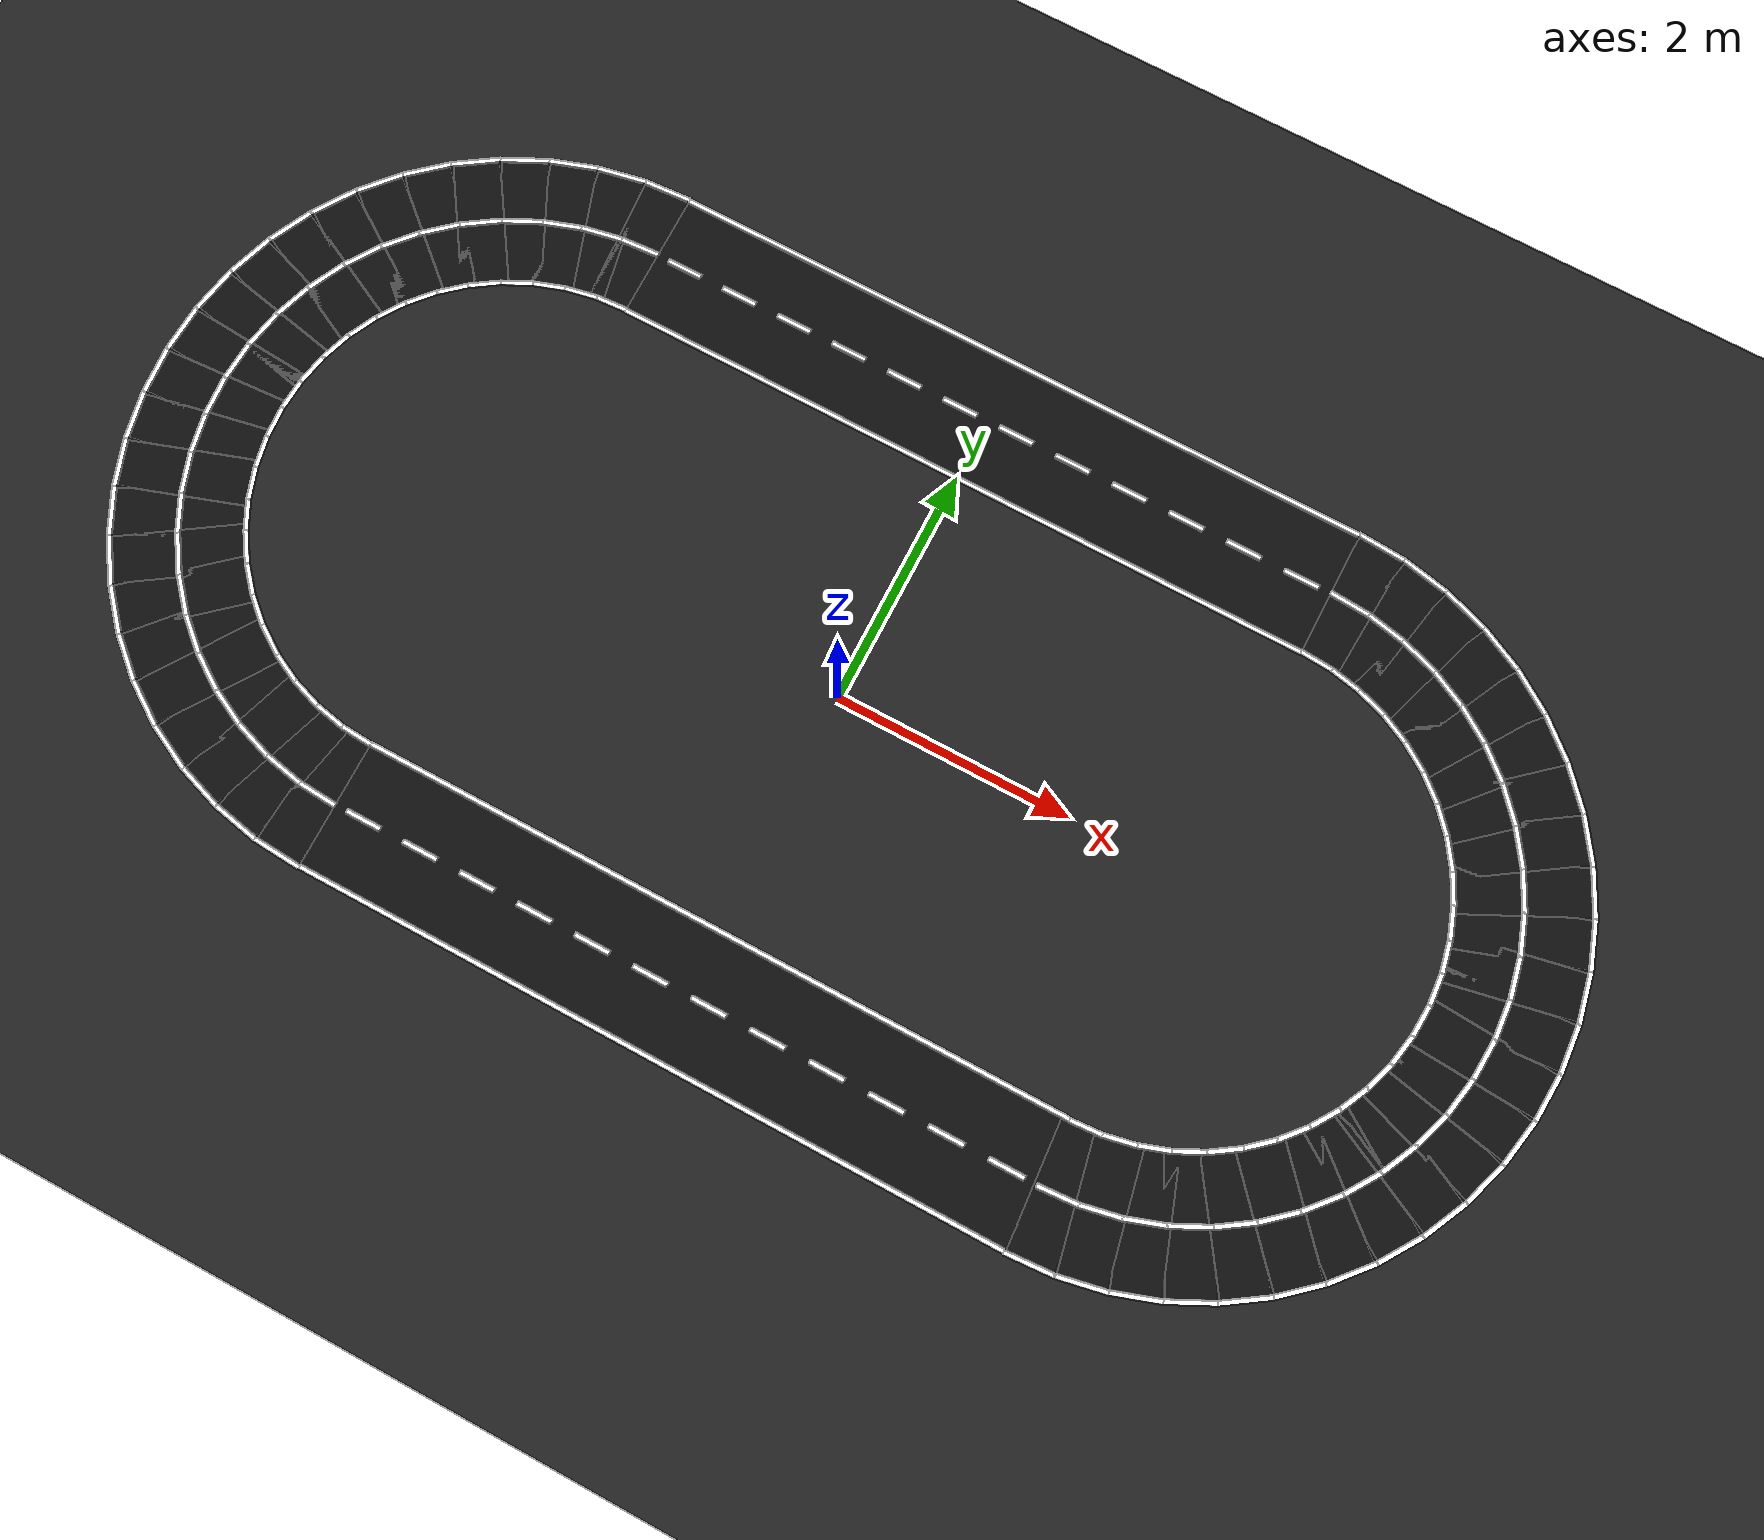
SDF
<?xml version="1.0" ?>
<sdf version="1.6">
  <world name="oval_lane_world">

    <!-- Required Gazebo Sim system plugins (Harmonic / bullet-featherstone) -->
    <plugin filename="gz-sim-physics-system"
            name="gz::sim::systems::Physics"/>
    <plugin filename="gz-sim-user-commands-system"
            name="gz::sim::systems::UserCommands"/>
    <plugin filename="gz-sim-scene-broadcaster-system"
            name="gz::sim::systems::SceneBroadcaster"/>
    <plugin filename="gz-sim-imu-system"
            name="gz::sim::systems::Imu"/>

    <gravity>0 0 -9.8</gravity>

    <physics name="default_physics" default="true" type="bullet">
      <max_step_size>0.001</max_step_size>
      <real_time_factor>1.0</real_time_factor>
    </physics>

    <light type="directional" name="sun">
      <cast_shadows>true</cast_shadows>
      <pose>0 0 10 0 0 0</pose>
      <diffuse>0.9 0.9 0.9 1</diffuse>
      <specular>0.1 0.1 0.1 1</specular>
      <direction>-0.5 0.1 -0.9</direction>
    </light>

    <model name="ground_plane">
      <static>true</static>
      <link name="link">
        <collision name="collision">
          <geometry>
            <plane><normal>0 0 1</normal><size>100 100</size></plane>
          </geometry>
          <surface>
            <friction>
              <ode><mu>1.0</mu><mu2>1.0</mu2></ode>
            </friction>
          </surface>
        </collision>
        <visual name="visual">
          <geometry>
            <plane><normal>0 0 1</normal><size>100 100</size></plane>
          </geometry>
          <material>
            <ambient>0.10 0.10 0.10 1</ambient>
            <diffuse>0.12 0.12 0.12 1</diffuse>
          </material>
        </visual>
      </link>
    </model>
    <model name="road_top">
      <static>true</static>
      <pose>0.00000 2.53400 0.00250 0 0 0.00000</pose>
      <link name="link">
        <visual name="visual">
          <geometry><box><size>6.00000 1.06800 0.00500</size></box></geometry>
          <material>
            <ambient>0.030 0.030 0.030 1</ambient>
            <diffuse>0.050 0.050 0.050 1</diffuse>
            <specular>0.05 0.05 0.05 1</specular>
          </material>
        </visual>
      </link>
    </model>
    <model name="road_bot">
      <static>true</static>
      <pose>0.00000 -2.53400 0.00250 0 0 0.00000</pose>
      <link name="link">
        <visual name="visual">
          <geometry><box><size>6.00000 1.06800 0.00500</size></box></geometry>
          <material>
            <ambient>0.030 0.030 0.030 1</ambient>
            <diffuse>0.050 0.050 0.050 1</diffuse>
            <specular>0.05 0.05 0.05 1</specular>
          </material>
        </visual>
      </link>
    </model>
    <model name="sl_top_0">
      <static>true</static>
      <pose>0.00000 2.00000 0.00700 0 0 0.00000</pose>
      <link name="link">
        <visual name="visual">
          <geometry><box><size>6.00000 0.04000 0.00400</size></box></geometry>
          <material>
            <ambient>1.000 1.000 1.000 1</ambient>
            <diffuse>1.000 1.000 1.000 1</diffuse>
            <specular>0.05 0.05 0.05 1</specular>
          </material>
        </visual>
      </link>
    </model>
    <model name="sl_bot_0">
      <static>true</static>
      <pose>0.00000 -2.00000 0.00700 0 0 0.00000</pose>
      <link name="link">
        <visual name="visual">
          <geometry><box><size>6.00000 0.04000 0.00400</size></box></geometry>
          <material>
            <ambient>1.000 1.000 1.000 1</ambient>
            <diffuse>1.000 1.000 1.000 1</diffuse>
            <specular>0.05 0.05 0.05 1</specular>
          </material>
        </visual>
      </link>
    </model>
    <model name="dl_top_1_0">
      <static>true</static>
      <pose>-2.75000 2.53400 0.00700 0 0 0.00000</pose>
      <link name="link">
        <visual name="visual">
          <geometry><box><size>0.30000 0.04000 0.00400</size></box></geometry>
          <material>
            <ambient>1.000 1.000 1.000 1</ambient>
            <diffuse>1.000 1.000 1.000 1</diffuse>
            <specular>0.05 0.05 0.05 1</specular>
          </material>
        </visual>
      </link>
    </model>
    <model name="dl_top_1_1">
      <static>true</static>
      <pose>-2.25000 2.53400 0.00700 0 0 0.00000</pose>
      <link name="link">
        <visual name="visual">
          <geometry><box><size>0.30000 0.04000 0.00400</size></box></geometry>
          <material>
            <ambient>1.000 1.000 1.000 1</ambient>
            <diffuse>1.000 1.000 1.000 1</diffuse>
            <specular>0.05 0.05 0.05 1</specular>
          </material>
        </visual>
      </link>
    </model>
    <model name="dl_top_1_2">
      <static>true</static>
      <pose>-1.75000 2.53400 0.00700 0 0 0.00000</pose>
      <link name="link">
        <visual name="visual">
          <geometry><box><size>0.30000 0.04000 0.00400</size></box></geometry>
          <material>
            <ambient>1.000 1.000 1.000 1</ambient>
            <diffuse>1.000 1.000 1.000 1</diffuse>
            <specular>0.05 0.05 0.05 1</specular>
          </material>
        </visual>
      </link>
    </model>
    <model name="dl_top_1_3">
      <static>true</static>
      <pose>-1.25000 2.53400 0.00700 0 0 0.00000</pose>
      <link name="link">
        <visual name="visual">
          <geometry><box><size>0.30000 0.04000 0.00400</size></box></geometry>
          <material>
            <ambient>1.000 1.000 1.000 1</ambient>
            <diffuse>1.000 1.000 1.000 1</diffuse>
            <specular>0.05 0.05 0.05 1</specular>
          </material>
        </visual>
      </link>
    </model>
    <model name="dl_top_1_4">
      <static>true</static>
      <pose>-0.75000 2.53400 0.00700 0 0 0.00000</pose>
      <link name="link">
        <visual name="visual">
          <geometry><box><size>0.30000 0.04000 0.00400</size></box></geometry>
          <material>
            <ambient>1.000 1.000 1.000 1</ambient>
            <diffuse>1.000 1.000 1.000 1</diffuse>
            <specular>0.05 0.05 0.05 1</specular>
          </material>
        </visual>
      </link>
    </model>
    <model name="dl_top_1_5">
      <static>true</static>
      <pose>-0.25000 2.53400 0.00700 0 0 0.00000</pose>
      <link name="link">
        <visual name="visual">
          <geometry><box><size>0.30000 0.04000 0.00400</size></box></geometry>
          <material>
            <ambient>1.000 1.000 1.000 1</ambient>
            <diffuse>1.000 1.000 1.000 1</diffuse>
            <specular>0.05 0.05 0.05 1</specular>
          </material>
        </visual>
      </link>
    </model>
    <model name="dl_top_1_6">
      <static>true</static>
      <pose>0.25000 2.53400 0.00700 0 0 0.00000</pose>
      <link name="link">
        <visual name="visual">
          <geometry><box><size>0.30000 0.04000 0.00400</size></box></geometry>
          <material>
            <ambient>1.000 1.000 1.000 1</ambient>
            <diffuse>1.000 1.000 1.000 1</diffuse>
            <specular>0.05 0.05 0.05 1</specular>
          </material>
        </visual>
      </link>
    </model>
    <model name="dl_top_1_7">
      <static>true</static>
      <pose>0.75000 2.53400 0.00700 0 0 0.00000</pose>
      <link name="link">
        <visual name="visual">
          <geometry><box><size>0.30000 0.04000 0.00400</size></box></geometry>
          <material>
            <ambient>1.000 1.000 1.000 1</ambient>
            <diffuse>1.000 1.000 1.000 1</diffuse>
            <specular>0.05 0.05 0.05 1</specular>
          </material>
        </visual>
      </link>
    </model>
    <model name="dl_top_1_8">
      <static>true</static>
      <pose>1.25000 2.53400 0.00700 0 0 0.00000</pose>
      <link name="link">
        <visual name="visual">
          <geometry><box><size>0.30000 0.04000 0.00400</size></box></geometry>
          <material>
            <ambient>1.000 1.000 1.000 1</ambient>
            <diffuse>1.000 1.000 1.000 1</diffuse>
            <specular>0.05 0.05 0.05 1</specular>
          </material>
        </visual>
      </link>
    </model>
    <model name="dl_top_1_9">
      <static>true</static>
      <pose>1.75000 2.53400 0.00700 0 0 0.00000</pose>
      <link name="link">
        <visual name="visual">
          <geometry><box><size>0.30000 0.04000 0.00400</size></box></geometry>
          <material>
            <ambient>1.000 1.000 1.000 1</ambient>
            <diffuse>1.000 1.000 1.000 1</diffuse>
            <specular>0.05 0.05 0.05 1</specular>
          </material>
        </visual>
      </link>
    </model>
    <model name="dl_top_1_10">
      <static>true</static>
      <pose>2.25000 2.53400 0.00700 0 0 0.00000</pose>
      <link name="link">
        <visual name="visual">
          <geometry><box><size>0.30000 0.04000 0.00400</size></box></geometry>
          <material>
            <ambient>1.000 1.000 1.000 1</ambient>
            <diffuse>1.000 1.000 1.000 1</diffuse>
            <specular>0.05 0.05 0.05 1</specular>
          </material>
        </visual>
      </link>
    </model>
    <model name="dl_top_1_11">
      <static>true</static>
      <pose>2.75000 2.53400 0.00700 0 0 0.00000</pose>
      <link name="link">
        <visual name="visual">
          <geometry><box><size>0.30000 0.04000 0.00400</size></box></geometry>
          <material>
            <ambient>1.000 1.000 1.000 1</ambient>
            <diffuse>1.000 1.000 1.000 1</diffuse>
            <specular>0.05 0.05 0.05 1</specular>
          </material>
        </visual>
      </link>
    </model>
    <model name="dl_bot_1_0">
      <static>true</static>
      <pose>-2.75000 -2.53400 0.00700 0 0 0.00000</pose>
      <link name="link">
        <visual name="visual">
          <geometry><box><size>0.30000 0.04000 0.00400</size></box></geometry>
          <material>
            <ambient>1.000 1.000 1.000 1</ambient>
            <diffuse>1.000 1.000 1.000 1</diffuse>
            <specular>0.05 0.05 0.05 1</specular>
          </material>
        </visual>
      </link>
    </model>
    <model name="dl_bot_1_1">
      <static>true</static>
      <pose>-2.25000 -2.53400 0.00700 0 0 0.00000</pose>
      <link name="link">
        <visual name="visual">
          <geometry><box><size>0.30000 0.04000 0.00400</size></box></geometry>
          <material>
            <ambient>1.000 1.000 1.000 1</ambient>
            <diffuse>1.000 1.000 1.000 1</diffuse>
            <specular>0.05 0.05 0.05 1</specular>
          </material>
        </visual>
      </link>
    </model>
    <model name="dl_bot_1_2">
      <static>true</static>
      <pose>-1.75000 -2.53400 0.00700 0 0 0.00000</pose>
      <link name="link">
        <visual name="visual">
          <geometry><box><size>0.30000 0.04000 0.00400</size></box></geometry>
          <material>
            <ambient>1.000 1.000 1.000 1</ambient>
            <diffuse>1.000 1.000 1.000 1</diffuse>
            <specular>0.05 0.05 0.05 1</specular>
          </material>
        </visual>
      </link>
    </model>
    <model name="dl_bot_1_3">
      <static>true</static>
      <pose>-1.25000 -2.53400 0.00700 0 0 0.00000</pose>
      <link name="link">
        <visual name="visual">
          <geometry><box><size>0.30000 0.04000 0.00400</size></box></geometry>
          <material>
            <ambient>1.000 1.000 1.000 1</ambient>
            <diffuse>1.000 1.000 1.000 1</diffuse>
            <specular>0.05 0.05 0.05 1</specular>
          </material>
        </visual>
      </link>
    </model>
    <model name="dl_bot_1_4">
      <static>true</static>
      <pose>-0.75000 -2.53400 0.00700 0 0 0.00000</pose>
      <link name="link">
        <visual name="visual">
          <geometry><box><size>0.30000 0.04000 0.00400</size></box></geometry>
          <material>
            <ambient>1.000 1.000 1.000 1</ambient>
            <diffuse>1.000 1.000 1.000 1</diffuse>
            <specular>0.05 0.05 0.05 1</specular>
          </material>
        </visual>
      </link>
    </model>
    <model name="dl_bot_1_5">
      <static>true</static>
      <pose>-0.25000 -2.53400 0.00700 0 0 0.00000</pose>
      <link name="link">
        <visual name="visual">
          <geometry><box><size>0.30000 0.04000 0.00400</size></box></geometry>
          <material>
            <ambient>1.000 1.000 1.000 1</ambient>
            <diffuse>1.000 1.000 1.000 1</diffuse>
            <specular>0.05 0.05 0.05 1</specular>
          </material>
        </visual>
      </link>
    </model>
    <model name="dl_bot_1_6">
      <static>true</static>
      <pose>0.25000 -2.53400 0.00700 0 0 0.00000</pose>
      <link name="link">
        <visual name="visual">
          <geometry><box><size>0.30000 0.04000 0.00400</size></box></geometry>
          <material>
            <ambient>1.000 1.000 1.000 1</ambient>
            <diffuse>1.000 1.000 1.000 1</diffuse>
            <specular>0.05 0.05 0.05 1</specular>
          </material>
        </visual>
      </link>
    </model>
    <model name="dl_bot_1_7">
      <static>true</static>
      <pose>0.75000 -2.53400 0.00700 0 0 0.00000</pose>
      <link name="link">
        <visual name="visual">
          <geometry><box><size>0.30000 0.04000 0.00400</size></box></geometry>
          <material>
            <ambient>1.000 1.000 1.000 1</ambient>
            <diffuse>1.000 1.000 1.000 1</diffuse>
            <specular>0.05 0.05 0.05 1</specular>
          </material>
        </visual>
      </link>
    </model>
    <model name="dl_bot_1_8">
      <static>true</static>
      <pose>1.25000 -2.53400 0.00700 0 0 0.00000</pose>
      <link name="link">
        <visual name="visual">
          <geometry><box><size>0.30000 0.04000 0.00400</size></box></geometry>
          <material>
            <ambient>1.000 1.000 1.000 1</ambient>
            <diffuse>1.000 1.000 1.000 1</diffuse>
            <specular>0.05 0.05 0.05 1</specular>
          </material>
        </visual>
      </link>
    </model>
    <model name="dl_bot_1_9">
      <static>true</static>
      <pose>1.75000 -2.53400 0.00700 0 0 0.00000</pose>
      <link name="link">
        <visual name="visual">
          <geometry><box><size>0.30000 0.04000 0.00400</size></box></geometry>
          <material>
            <ambient>1.000 1.000 1.000 1</ambient>
            <diffuse>1.000 1.000 1.000 1</diffuse>
            <specular>0.05 0.05 0.05 1</specular>
          </material>
        </visual>
      </link>
    </model>
    <model name="dl_bot_1_10">
      <static>true</static>
      <pose>2.25000 -2.53400 0.00700 0 0 0.00000</pose>
      <link name="link">
        <visual name="visual">
          <geometry><box><size>0.30000 0.04000 0.00400</size></box></geometry>
          <material>
            <ambient>1.000 1.000 1.000 1</ambient>
            <diffuse>1.000 1.000 1.000 1</diffuse>
            <specular>0.05 0.05 0.05 1</specular>
          </material>
        </visual>
      </link>
    </model>
    <model name="dl_bot_1_11">
      <static>true</static>
      <pose>2.75000 -2.53400 0.00700 0 0 0.00000</pose>
      <link name="link">
        <visual name="visual">
          <geometry><box><size>0.30000 0.04000 0.00400</size></box></geometry>
          <material>
            <ambient>1.000 1.000 1.000 1</ambient>
            <diffuse>1.000 1.000 1.000 1</diffuse>
            <specular>0.05 0.05 0.05 1</specular>
          </material>
        </visual>
      </link>
    </model>
    <model name="sl_top_2">
      <static>true</static>
      <pose>0.00000 3.06800 0.00700 0 0 0.00000</pose>
      <link name="link">
        <visual name="visual">
          <geometry><box><size>6.00000 0.04000 0.00400</size></box></geometry>
          <material>
            <ambient>1.000 1.000 1.000 1</ambient>
            <diffuse>1.000 1.000 1.000 1</diffuse>
            <specular>0.05 0.05 0.05 1</specular>
          </material>
        </visual>
      </link>
    </model>
    <model name="sl_bot_2">
      <static>true</static>
      <pose>0.00000 -3.06800 0.00700 0 0 0.00000</pose>
      <link name="link">
        <visual name="visual">
          <geometry><box><size>6.00000 0.04000 0.00400</size></box></geometry>
          <material>
            <ambient>1.000 1.000 1.000 1</ambient>
            <diffuse>1.000 1.000 1.000 1</diffuse>
            <specular>0.05 0.05 0.05 1</specular>
          </material>
        </visual>
      </link>
    </model>
    <model name="road_r_0">
      <static>true</static>
      <pose>3.16524 2.52109 0.00250 0.0 0.0 -0.06545</pose>
      <link name="link">
        <visual name="visual">
          <geometry><box><size>0.38165 1.06800 0.00500</size></box></geometry>
          <material>
            <ambient>0.030 0.030 0.030 1</ambient>
            <diffuse>0.050 0.050 0.050 1</diffuse>
            <specular>0.05 0.05 0.05 1</specular>
          </material>
        </visual>
      </link>
    </model>
    <model name="cl_r_0_0">
      <static>true</static>
      <pose>3.13081 1.99572 0.00700 0 0 -0.06545</pose>
      <link name="link">
        <visual name="visual">
          <geometry><box><size>0.27180 0.04000 0.00400</size></box></geometry>
          <material>
            <ambient>1.000 1.000 1.000 1</ambient>
            <diffuse>1.000 1.000 1.000 1</diffuse>
            <specular>0.05 0.05 0.05 1</specular>
          </material>
        </visual>
      </link>
    </model>
    <model name="cl_r_1_0">
      <static>true</static>
      <pose>3.16573 2.52857 0.00700 0 0 -0.06545</pose>
      <link name="link">
        <visual name="visual">
          <geometry><box><size>0.34170 0.04000 0.00400</size></box></geometry>
          <material>
            <ambient>1.000 1.000 1.000 1</ambient>
            <diffuse>1.000 1.000 1.000 1</diffuse>
            <specular>0.05 0.05 0.05 1</specular>
          </material>
        </visual>
      </link>
    </model>
    <model name="cl_r_2_0">
      <static>true</static>
      <pose>3.20066 3.06143 0.00700 0 0 -0.06545</pose>
      <link name="link">
        <visual name="visual">
          <geometry><box><size>0.41160 0.04000 0.00400</size></box></geometry>
          <material>
            <ambient>1.000 1.000 1.000 1</ambient>
            <diffuse>1.000 1.000 1.000 1</diffuse>
            <specular>0.05 0.05 0.05 1</specular>
          </material>
        </visual>
      </link>
    </model>
    <model name="road_r_1">
      <static>true</static>
      <pose>3.49290 2.47795 0.00250 0.0 0.0 -0.19635</pose>
      <link name="link">
        <visual name="visual">
          <geometry><box><size>0.38165 1.06800 0.00500</size></box></geometry>
          <material>
            <ambient>0.030 0.030 0.030 1</ambient>
            <diffuse>0.050 0.050 0.050 1</diffuse>
            <specular>0.05 0.05 0.05 1</specular>
          </material>
        </visual>
      </link>
    </model>
    <model name="cl_r_0_1">
      <static>true</static>
      <pose>3.39018 1.96157 0.00700 0 0 -0.19635</pose>
      <link name="link">
        <visual name="visual">
          <geometry><box><size>0.27180 0.04000 0.00400</size></box></geometry>
          <material>
            <ambient>1.000 1.000 1.000 1</ambient>
            <diffuse>1.000 1.000 1.000 1</diffuse>
            <specular>0.05 0.05 0.05 1</specular>
          </material>
        </visual>
      </link>
    </model>
    <model name="cl_r_1_1">
      <static>true</static>
      <pose>3.49436 2.48531 0.00700 0 0 -0.19635</pose>
      <link name="link">
        <visual name="visual">
          <geometry><box><size>0.34170 0.04000 0.00400</size></box></geometry>
          <material>
            <ambient>1.000 1.000 1.000 1</ambient>
            <diffuse>1.000 1.000 1.000 1</diffuse>
            <specular>0.05 0.05 0.05 1</specular>
          </material>
        </visual>
      </link>
    </model>
    <model name="cl_r_2_1">
      <static>true</static>
      <pose>3.59854 3.00905 0.00700 0 0 -0.19635</pose>
      <link name="link">
        <visual name="visual">
          <geometry><box><size>0.41160 0.04000 0.00400</size></box></geometry>
          <material>
            <ambient>1.000 1.000 1.000 1</ambient>
            <diffuse>1.000 1.000 1.000 1</diffuse>
            <specular>0.05 0.05 0.05 1</specular>
          </material>
        </visual>
      </link>
    </model>
    <model name="road_r_2">
      <static>true</static>
      <pose>3.81211 2.39242 0.00250 0.0 0.0 -0.32725</pose>
      <link name="link">
        <visual name="visual">
          <geometry><box><size>0.38165 1.06800 0.00500</size></box></geometry>
          <material>
            <ambient>0.030 0.030 0.030 1</ambient>
            <diffuse>0.050 0.050 0.050 1</diffuse>
            <specular>0.05 0.05 0.05 1</specular>
          </material>
        </visual>
      </link>
    </model>
    <model name="cl_r_0_2">
      <static>true</static>
      <pose>3.64288 1.89386 0.00700 0 0 -0.32725</pose>
      <link name="link">
        <visual name="visual">
          <geometry><box><size>0.27180 0.04000 0.00400</size></box></geometry>
          <material>
            <ambient>1.000 1.000 1.000 1</ambient>
            <diffuse>1.000 1.000 1.000 1</diffuse>
            <specular>0.05 0.05 0.05 1</specular>
          </material>
        </visual>
      </link>
    </model>
    <model name="cl_r_1_2">
      <static>true</static>
      <pose>3.81453 2.39952 0.00700 0 0 -0.32725</pose>
      <link name="link">
        <visual name="visual">
          <geometry><box><size>0.34170 0.04000 0.00400</size></box></geometry>
          <material>
            <ambient>1.000 1.000 1.000 1</ambient>
            <diffuse>1.000 1.000 1.000 1</diffuse>
            <specular>0.05 0.05 0.05 1</specular>
          </material>
        </visual>
      </link>
    </model>
    <model name="cl_r_2_2">
      <static>true</static>
      <pose>3.98617 2.90518 0.00700 0 0 -0.32725</pose>
      <link name="link">
        <visual name="visual">
          <geometry><box><size>0.41160 0.04000 0.00400</size></box></geometry>
          <material>
            <ambient>1.000 1.000 1.000 1</ambient>
            <diffuse>1.000 1.000 1.000 1</diffuse>
            <specular>0.05 0.05 0.05 1</specular>
          </material>
        </visual>
      </link>
    </model>
    <model name="road_r_3">
      <static>true</static>
      <pose>4.11744 2.26595 0.00250 0.0 0.0 -0.45815</pose>
      <link name="link">
        <visual name="visual">
          <geometry><box><size>0.38165 1.06800 0.00500</size></box></geometry>
          <material>
            <ambient>0.030 0.030 0.030 1</ambient>
            <diffuse>0.050 0.050 0.050 1</diffuse>
            <specular>0.05 0.05 0.05 1</specular>
          </material>
        </visual>
      </link>
    </model>
    <model name="cl_r_0_3">
      <static>true</static>
      <pose>3.88458 1.79375 0.00700 0 0 -0.45815</pose>
      <link name="link">
        <visual name="visual">
          <geometry><box><size>0.27180 0.04000 0.00400</size></box></geometry>
          <material>
            <ambient>1.000 1.000 1.000 1</ambient>
            <diffuse>1.000 1.000 1.000 1</diffuse>
            <specular>0.05 0.05 0.05 1</specular>
          </material>
        </visual>
      </link>
    </model>
    <model name="cl_r_1_3">
      <static>true</static>
      <pose>4.12076 2.27268 0.00700 0 0 -0.45815</pose>
      <link name="link">
        <visual name="visual">
          <geometry><box><size>0.34170 0.04000 0.00400</size></box></geometry>
          <material>
            <ambient>1.000 1.000 1.000 1</ambient>
            <diffuse>1.000 1.000 1.000 1</diffuse>
            <specular>0.05 0.05 0.05 1</specular>
          </material>
        </visual>
      </link>
    </model>
    <model name="cl_r_2_3">
      <static>true</static>
      <pose>4.35694 2.75161 0.00700 0 0 -0.45815</pose>
      <link name="link">
        <visual name="visual">
          <geometry><box><size>0.41160 0.04000 0.00400</size></box></geometry>
          <material>
            <ambient>1.000 1.000 1.000 1</ambient>
            <diffuse>1.000 1.000 1.000 1</diffuse>
            <specular>0.05 0.05 0.05 1</specular>
          </material>
        </visual>
      </link>
    </model>
    <model name="road_r_4">
      <static>true</static>
      <pose>4.40365 2.10071 0.00250 0.0 0.0 -0.58905</pose>
      <link name="link">
        <visual name="visual">
          <geometry><box><size>0.38165 1.06800 0.00500</size></box></geometry>
          <material>
            <ambient>0.030 0.030 0.030 1</ambient>
            <diffuse>0.050 0.050 0.050 1</diffuse>
            <specular>0.05 0.05 0.05 1</specular>
          </material>
        </visual>
      </link>
    </model>
    <model name="cl_r_0_4">
      <static>true</static>
      <pose>4.11114 1.66294 0.00700 0 0 -0.58905</pose>
      <link name="link">
        <visual name="visual">
          <geometry><box><size>0.27180 0.04000 0.00400</size></box></geometry>
          <material>
            <ambient>1.000 1.000 1.000 1</ambient>
            <diffuse>1.000 1.000 1.000 1</diffuse>
            <specular>0.05 0.05 0.05 1</specular>
          </material>
        </visual>
      </link>
    </model>
    <model name="cl_r_1_4">
      <static>true</static>
      <pose>4.40781 2.10694 0.00700 0 0 -0.58905</pose>
      <link name="link">
        <visual name="visual">
          <geometry><box><size>0.34170 0.04000 0.00400</size></box></geometry>
          <material>
            <ambient>1.000 1.000 1.000 1</ambient>
            <diffuse>1.000 1.000 1.000 1</diffuse>
            <specular>0.05 0.05 0.05 1</specular>
          </material>
        </visual>
      </link>
    </model>
    <model name="cl_r_2_4">
      <static>true</static>
      <pose>4.70449 2.55095 0.00700 0 0 -0.58905</pose>
      <link name="link">
        <visual name="visual">
          <geometry><box><size>0.41160 0.04000 0.00400</size></box></geometry>
          <material>
            <ambient>1.000 1.000 1.000 1</ambient>
            <diffuse>1.000 1.000 1.000 1</diffuse>
            <specular>0.05 0.05 0.05 1</specular>
          </material>
        </visual>
      </link>
    </model>
    <model name="road_r_5">
      <static>true</static>
      <pose>4.66584 1.89952 0.00250 0.0 0.0 -0.71995</pose>
      <link name="link">
        <visual name="visual">
          <geometry><box><size>0.38165 1.06800 0.00500</size></box></geometry>
          <material>
            <ambient>0.030 0.030 0.030 1</ambient>
            <diffuse>0.050 0.050 0.050 1</diffuse>
            <specular>0.05 0.05 0.05 1</specular>
          </material>
        </visual>
      </link>
    </model>
    <model name="cl_r_0_5">
      <static>true</static>
      <pose>4.31869 1.50368 0.00700 0 0 -0.71995</pose>
      <link name="link">
        <visual name="visual">
          <geometry><box><size>0.27180 0.04000 0.00400</size></box></geometry>
          <material>
            <ambient>1.000 1.000 1.000 1</ambient>
            <diffuse>1.000 1.000 1.000 1</diffuse>
            <specular>0.05 0.05 0.05 1</specular>
          </material>
        </visual>
      </link>
    </model>
    <model name="cl_r_1_5">
      <static>true</static>
      <pose>4.67078 1.90516 0.00700 0 0 -0.71995</pose>
      <link name="link">
        <visual name="visual">
          <geometry><box><size>0.34170 0.04000 0.00400</size></box></geometry>
          <material>
            <ambient>1.000 1.000 1.000 1</ambient>
            <diffuse>1.000 1.000 1.000 1</diffuse>
            <specular>0.05 0.05 0.05 1</specular>
          </material>
        </visual>
      </link>
    </model>
    <model name="cl_r_2_5">
      <static>true</static>
      <pose>5.02287 2.30664 0.00700 0 0 -0.71995</pose>
      <link name="link">
        <visual name="visual">
          <geometry><box><size>0.41160 0.04000 0.00400</size></box></geometry>
          <material>
            <ambient>1.000 1.000 1.000 1</ambient>
            <diffuse>1.000 1.000 1.000 1</diffuse>
            <specular>0.05 0.05 0.05 1</specular>
          </material>
        </visual>
      </link>
    </model>
    <model name="road_r_6">
      <static>true</static>
      <pose>4.89952 1.66584 0.00250 0.0 0.0 -0.85085</pose>
      <link name="link">
        <visual name="visual">
          <geometry><box><size>0.38165 1.06800 0.00500</size></box></geometry>
          <material>
            <ambient>0.030 0.030 0.030 1</ambient>
            <diffuse>0.050 0.050 0.050 1</diffuse>
            <specular>0.05 0.05 0.05 1</specular>
          </material>
        </visual>
      </link>
    </model>
    <model name="cl_r_0_6">
      <static>true</static>
      <pose>4.50368 1.31869 0.00700 0 0 -0.85085</pose>
      <link name="link">
        <visual name="visual">
          <geometry><box><size>0.27180 0.04000 0.00400</size></box></geometry>
          <material>
            <ambient>1.000 1.000 1.000 1</ambient>
            <diffuse>1.000 1.000 1.000 1</diffuse>
            <specular>0.05 0.05 0.05 1</specular>
          </material>
        </visual>
      </link>
    </model>
    <model name="cl_r_1_6">
      <static>true</static>
      <pose>4.90516 1.67078 0.00700 0 0 -0.85085</pose>
      <link name="link">
        <visual name="visual">
          <geometry><box><size>0.34170 0.04000 0.00400</size></box></geometry>
          <material>
            <ambient>1.000 1.000 1.000 1</ambient>
            <diffuse>1.000 1.000 1.000 1</diffuse>
            <specular>0.05 0.05 0.05 1</specular>
          </material>
        </visual>
      </link>
    </model>
    <model name="cl_r_2_6">
      <static>true</static>
      <pose>5.30665 2.02287 0.00700 0 0 -0.85085</pose>
      <link name="link">
        <visual name="visual">
          <geometry><box><size>0.41160 0.04000 0.00400</size></box></geometry>
          <material>
            <ambient>1.000 1.000 1.000 1</ambient>
            <diffuse>1.000 1.000 1.000 1</diffuse>
            <specular>0.05 0.05 0.05 1</specular>
          </material>
        </visual>
      </link>
    </model>
    <model name="road_r_7">
      <static>true</static>
      <pose>5.10071 1.40365 0.00250 0.0 0.0 -0.98175</pose>
      <link name="link">
        <visual name="visual">
          <geometry><box><size>0.38165 1.06800 0.00500</size></box></geometry>
          <material>
            <ambient>0.030 0.030 0.030 1</ambient>
            <diffuse>0.050 0.050 0.050 1</diffuse>
            <specular>0.05 0.05 0.05 1</specular>
          </material>
        </visual>
      </link>
    </model>
    <model name="cl_r_0_7">
      <static>true</static>
      <pose>4.66294 1.11114 0.00700 0 0 -0.98175</pose>
      <link name="link">
        <visual name="visual">
          <geometry><box><size>0.27180 0.04000 0.00400</size></box></geometry>
          <material>
            <ambient>1.000 1.000 1.000 1</ambient>
            <diffuse>1.000 1.000 1.000 1</diffuse>
            <specular>0.05 0.05 0.05 1</specular>
          </material>
        </visual>
      </link>
    </model>
    <model name="cl_r_1_7">
      <static>true</static>
      <pose>5.10694 1.40781 0.00700 0 0 -0.98175</pose>
      <link name="link">
        <visual name="visual">
          <geometry><box><size>0.34170 0.04000 0.00400</size></box></geometry>
          <material>
            <ambient>1.000 1.000 1.000 1</ambient>
            <diffuse>1.000 1.000 1.000 1</diffuse>
            <specular>0.05 0.05 0.05 1</specular>
          </material>
        </visual>
      </link>
    </model>
    <model name="cl_r_2_7">
      <static>true</static>
      <pose>5.55095 1.70449 0.00700 0 0 -0.98175</pose>
      <link name="link">
        <visual name="visual">
          <geometry><box><size>0.41160 0.04000 0.00400</size></box></geometry>
          <material>
            <ambient>1.000 1.000 1.000 1</ambient>
            <diffuse>1.000 1.000 1.000 1</diffuse>
            <specular>0.05 0.05 0.05 1</specular>
          </material>
        </visual>
      </link>
    </model>
    <model name="road_r_8">
      <static>true</static>
      <pose>5.26595 1.11744 0.00250 0.0 0.0 -1.11265</pose>
      <link name="link">
        <visual name="visual">
          <geometry><box><size>0.38165 1.06800 0.00500</size></box></geometry>
          <material>
            <ambient>0.030 0.030 0.030 1</ambient>
            <diffuse>0.050 0.050 0.050 1</diffuse>
            <specular>0.05 0.05 0.05 1</specular>
          </material>
        </visual>
      </link>
    </model>
    <model name="cl_r_0_8">
      <static>true</static>
      <pose>4.79375 0.88458 0.00700 0 0 -1.11265</pose>
      <link name="link">
        <visual name="visual">
          <geometry><box><size>0.27180 0.04000 0.00400</size></box></geometry>
          <material>
            <ambient>1.000 1.000 1.000 1</ambient>
            <diffuse>1.000 1.000 1.000 1</diffuse>
            <specular>0.05 0.05 0.05 1</specular>
          </material>
        </visual>
      </link>
    </model>
    <model name="cl_r_1_8">
      <static>true</static>
      <pose>5.27268 1.12076 0.00700 0 0 -1.11265</pose>
      <link name="link">
        <visual name="visual">
          <geometry><box><size>0.34170 0.04000 0.00400</size></box></geometry>
          <material>
            <ambient>1.000 1.000 1.000 1</ambient>
            <diffuse>1.000 1.000 1.000 1</diffuse>
            <specular>0.05 0.05 0.05 1</specular>
          </material>
        </visual>
      </link>
    </model>
    <model name="cl_r_2_8">
      <static>true</static>
      <pose>5.75161 1.35694 0.00700 0 0 -1.11265</pose>
      <link name="link">
        <visual name="visual">
          <geometry><box><size>0.41160 0.04000 0.00400</size></box></geometry>
          <material>
            <ambient>1.000 1.000 1.000 1</ambient>
            <diffuse>1.000 1.000 1.000 1</diffuse>
            <specular>0.05 0.05 0.05 1</specular>
          </material>
        </visual>
      </link>
    </model>
    <model name="road_r_9">
      <static>true</static>
      <pose>5.39242 0.81212 0.00250 0.0 0.0 -1.24355</pose>
      <link name="link">
        <visual name="visual">
          <geometry><box><size>0.38165 1.06800 0.00500</size></box></geometry>
          <material>
            <ambient>0.030 0.030 0.030 1</ambient>
            <diffuse>0.050 0.050 0.050 1</diffuse>
            <specular>0.05 0.05 0.05 1</specular>
          </material>
        </visual>
      </link>
    </model>
    <model name="cl_r_0_9">
      <static>true</static>
      <pose>4.89386 0.64288 0.00700 0 0 -1.24355</pose>
      <link name="link">
        <visual name="visual">
          <geometry><box><size>0.27180 0.04000 0.00400</size></box></geometry>
          <material>
            <ambient>1.000 1.000 1.000 1</ambient>
            <diffuse>1.000 1.000 1.000 1</diffuse>
            <specular>0.05 0.05 0.05 1</specular>
          </material>
        </visual>
      </link>
    </model>
    <model name="cl_r_1_9">
      <static>true</static>
      <pose>5.39952 0.81453 0.00700 0 0 -1.24355</pose>
      <link name="link">
        <visual name="visual">
          <geometry><box><size>0.34170 0.04000 0.00400</size></box></geometry>
          <material>
            <ambient>1.000 1.000 1.000 1</ambient>
            <diffuse>1.000 1.000 1.000 1</diffuse>
            <specular>0.05 0.05 0.05 1</specular>
          </material>
        </visual>
      </link>
    </model>
    <model name="cl_r_2_9">
      <static>true</static>
      <pose>5.90518 0.98618 0.00700 0 0 -1.24355</pose>
      <link name="link">
        <visual name="visual">
          <geometry><box><size>0.41160 0.04000 0.00400</size></box></geometry>
          <material>
            <ambient>1.000 1.000 1.000 1</ambient>
            <diffuse>1.000 1.000 1.000 1</diffuse>
            <specular>0.05 0.05 0.05 1</specular>
          </material>
        </visual>
      </link>
    </model>
    <model name="road_r_10">
      <static>true</static>
      <pose>5.47795 0.49290 0.00250 0.0 0.0 -1.37445</pose>
      <link name="link">
        <visual name="visual">
          <geometry><box><size>0.38165 1.06800 0.00500</size></box></geometry>
          <material>
            <ambient>0.030 0.030 0.030 1</ambient>
            <diffuse>0.050 0.050 0.050 1</diffuse>
            <specular>0.05 0.05 0.05 1</specular>
          </material>
        </visual>
      </link>
    </model>
    <model name="cl_r_0_10">
      <static>true</static>
      <pose>4.96157 0.39018 0.00700 0 0 -1.37445</pose>
      <link name="link">
        <visual name="visual">
          <geometry><box><size>0.27180 0.04000 0.00400</size></box></geometry>
          <material>
            <ambient>1.000 1.000 1.000 1</ambient>
            <diffuse>1.000 1.000 1.000 1</diffuse>
            <specular>0.05 0.05 0.05 1</specular>
          </material>
        </visual>
      </link>
    </model>
    <model name="cl_r_1_10">
      <static>true</static>
      <pose>5.48531 0.49436 0.00700 0 0 -1.37445</pose>
      <link name="link">
        <visual name="visual">
          <geometry><box><size>0.34170 0.04000 0.00400</size></box></geometry>
          <material>
            <ambient>1.000 1.000 1.000 1</ambient>
            <diffuse>1.000 1.000 1.000 1</diffuse>
            <specular>0.05 0.05 0.05 1</specular>
          </material>
        </visual>
      </link>
    </model>
    <model name="cl_r_2_10">
      <static>true</static>
      <pose>6.00905 0.59854 0.00700 0 0 -1.37445</pose>
      <link name="link">
        <visual name="visual">
          <geometry><box><size>0.41160 0.04000 0.00400</size></box></geometry>
          <material>
            <ambient>1.000 1.000 1.000 1</ambient>
            <diffuse>1.000 1.000 1.000 1</diffuse>
            <specular>0.05 0.05 0.05 1</specular>
          </material>
        </visual>
      </link>
    </model>
    <model name="road_r_11">
      <static>true</static>
      <pose>5.52109 0.16524 0.00250 0.0 0.0 -1.50535</pose>
      <link name="link">
        <visual name="visual">
          <geometry><box><size>0.38165 1.06800 0.00500</size></box></geometry>
          <material>
            <ambient>0.030 0.030 0.030 1</ambient>
            <diffuse>0.050 0.050 0.050 1</diffuse>
            <specular>0.05 0.05 0.05 1</specular>
          </material>
        </visual>
      </link>
    </model>
    <model name="cl_r_0_11">
      <static>true</static>
      <pose>4.99572 0.13081 0.00700 0 0 -1.50535</pose>
      <link name="link">
        <visual name="visual">
          <geometry><box><size>0.27180 0.04000 0.00400</size></box></geometry>
          <material>
            <ambient>1.000 1.000 1.000 1</ambient>
            <diffuse>1.000 1.000 1.000 1</diffuse>
            <specular>0.05 0.05 0.05 1</specular>
          </material>
        </visual>
      </link>
    </model>
    <model name="cl_r_1_11">
      <static>true</static>
      <pose>5.52858 0.16573 0.00700 0 0 -1.50535</pose>
      <link name="link">
        <visual name="visual">
          <geometry><box><size>0.34170 0.04000 0.00400</size></box></geometry>
          <material>
            <ambient>1.000 1.000 1.000 1</ambient>
            <diffuse>1.000 1.000 1.000 1</diffuse>
            <specular>0.05 0.05 0.05 1</specular>
          </material>
        </visual>
      </link>
    </model>
    <model name="cl_r_2_11">
      <static>true</static>
      <pose>6.06143 0.20066 0.00700 0 0 -1.50535</pose>
      <link name="link">
        <visual name="visual">
          <geometry><box><size>0.41160 0.04000 0.00400</size></box></geometry>
          <material>
            <ambient>1.000 1.000 1.000 1</ambient>
            <diffuse>1.000 1.000 1.000 1</diffuse>
            <specular>0.05 0.05 0.05 1</specular>
          </material>
        </visual>
      </link>
    </model>
    <model name="road_r_12">
      <static>true</static>
      <pose>5.52109 -0.16524 0.00250 0.0 0.0 -1.63625</pose>
      <link name="link">
        <visual name="visual">
          <geometry><box><size>0.38165 1.06800 0.00500</size></box></geometry>
          <material>
            <ambient>0.030 0.030 0.030 1</ambient>
            <diffuse>0.050 0.050 0.050 1</diffuse>
            <specular>0.05 0.05 0.05 1</specular>
          </material>
        </visual>
      </link>
    </model>
    <model name="cl_r_0_12">
      <static>true</static>
      <pose>4.99572 -0.13081 0.00700 0 0 -1.63625</pose>
      <link name="link">
        <visual name="visual">
          <geometry><box><size>0.27180 0.04000 0.00400</size></box></geometry>
          <material>
            <ambient>1.000 1.000 1.000 1</ambient>
            <diffuse>1.000 1.000 1.000 1</diffuse>
            <specular>0.05 0.05 0.05 1</specular>
          </material>
        </visual>
      </link>
    </model>
    <model name="cl_r_1_12">
      <static>true</static>
      <pose>5.52857 -0.16573 0.00700 0 0 -1.63625</pose>
      <link name="link">
        <visual name="visual">
          <geometry><box><size>0.34170 0.04000 0.00400</size></box></geometry>
          <material>
            <ambient>1.000 1.000 1.000 1</ambient>
            <diffuse>1.000 1.000 1.000 1</diffuse>
            <specular>0.05 0.05 0.05 1</specular>
          </material>
        </visual>
      </link>
    </model>
    <model name="cl_r_2_12">
      <static>true</static>
      <pose>6.06143 -0.20066 0.00700 0 0 -1.63625</pose>
      <link name="link">
        <visual name="visual">
          <geometry><box><size>0.41160 0.04000 0.00400</size></box></geometry>
          <material>
            <ambient>1.000 1.000 1.000 1</ambient>
            <diffuse>1.000 1.000 1.000 1</diffuse>
            <specular>0.05 0.05 0.05 1</specular>
          </material>
        </visual>
      </link>
    </model>
    <model name="road_r_13">
      <static>true</static>
      <pose>5.47795 -0.49290 0.00250 0.0 0.0 -1.76715</pose>
      <link name="link">
        <visual name="visual">
          <geometry><box><size>0.38165 1.06800 0.00500</size></box></geometry>
          <material>
            <ambient>0.030 0.030 0.030 1</ambient>
            <diffuse>0.050 0.050 0.050 1</diffuse>
            <specular>0.05 0.05 0.05 1</specular>
          </material>
        </visual>
      </link>
    </model>
    <model name="cl_r_0_13">
      <static>true</static>
      <pose>4.96157 -0.39018 0.00700 0 0 -1.76715</pose>
      <link name="link">
        <visual name="visual">
          <geometry><box><size>0.27180 0.04000 0.00400</size></box></geometry>
          <material>
            <ambient>1.000 1.000 1.000 1</ambient>
            <diffuse>1.000 1.000 1.000 1</diffuse>
            <specular>0.05 0.05 0.05 1</specular>
          </material>
        </visual>
      </link>
    </model>
    <model name="cl_r_1_13">
      <static>true</static>
      <pose>5.48531 -0.49436 0.00700 0 0 -1.76715</pose>
      <link name="link">
        <visual name="visual">
          <geometry><box><size>0.34170 0.04000 0.00400</size></box></geometry>
          <material>
            <ambient>1.000 1.000 1.000 1</ambient>
            <diffuse>1.000 1.000 1.000 1</diffuse>
            <specular>0.05 0.05 0.05 1</specular>
          </material>
        </visual>
      </link>
    </model>
    <model name="cl_r_2_13">
      <static>true</static>
      <pose>6.00905 -0.59854 0.00700 0 0 -1.76715</pose>
      <link name="link">
        <visual name="visual">
          <geometry><box><size>0.41160 0.04000 0.00400</size></box></geometry>
          <material>
            <ambient>1.000 1.000 1.000 1</ambient>
            <diffuse>1.000 1.000 1.000 1</diffuse>
            <specular>0.05 0.05 0.05 1</specular>
          </material>
        </visual>
      </link>
    </model>
    <model name="road_r_14">
      <static>true</static>
      <pose>5.39242 -0.81211 0.00250 0.0 0.0 -1.89805</pose>
      <link name="link">
        <visual name="visual">
          <geometry><box><size>0.38165 1.06800 0.00500</size></box></geometry>
          <material>
            <ambient>0.030 0.030 0.030 1</ambient>
            <diffuse>0.050 0.050 0.050 1</diffuse>
            <specular>0.05 0.05 0.05 1</specular>
          </material>
        </visual>
      </link>
    </model>
    <model name="cl_r_0_14">
      <static>true</static>
      <pose>4.89386 -0.64288 0.00700 0 0 -1.89805</pose>
      <link name="link">
        <visual name="visual">
          <geometry><box><size>0.27180 0.04000 0.00400</size></box></geometry>
          <material>
            <ambient>1.000 1.000 1.000 1</ambient>
            <diffuse>1.000 1.000 1.000 1</diffuse>
            <specular>0.05 0.05 0.05 1</specular>
          </material>
        </visual>
      </link>
    </model>
    <model name="cl_r_1_14">
      <static>true</static>
      <pose>5.39952 -0.81453 0.00700 0 0 -1.89805</pose>
      <link name="link">
        <visual name="visual">
          <geometry><box><size>0.34170 0.04000 0.00400</size></box></geometry>
          <material>
            <ambient>1.000 1.000 1.000 1</ambient>
            <diffuse>1.000 1.000 1.000 1</diffuse>
            <specular>0.05 0.05 0.05 1</specular>
          </material>
        </visual>
      </link>
    </model>
    <model name="cl_r_2_14">
      <static>true</static>
      <pose>5.90518 -0.98617 0.00700 0 0 -1.89805</pose>
      <link name="link">
        <visual name="visual">
          <geometry><box><size>0.41160 0.04000 0.00400</size></box></geometry>
          <material>
            <ambient>1.000 1.000 1.000 1</ambient>
            <diffuse>1.000 1.000 1.000 1</diffuse>
            <specular>0.05 0.05 0.05 1</specular>
          </material>
        </visual>
      </link>
    </model>
    <model name="road_r_15">
      <static>true</static>
      <pose>5.26595 -1.11744 0.00250 0.0 0.0 -2.02895</pose>
      <link name="link">
        <visual name="visual">
          <geometry><box><size>0.38165 1.06800 0.00500</size></box></geometry>
          <material>
            <ambient>0.030 0.030 0.030 1</ambient>
            <diffuse>0.050 0.050 0.050 1</diffuse>
            <specular>0.05 0.05 0.05 1</specular>
          </material>
        </visual>
      </link>
    </model>
    <model name="cl_r_0_15">
      <static>true</static>
      <pose>4.79375 -0.88458 0.00700 0 0 -2.02895</pose>
      <link name="link">
        <visual name="visual">
          <geometry><box><size>0.27180 0.04000 0.00400</size></box></geometry>
          <material>
            <ambient>1.000 1.000 1.000 1</ambient>
            <diffuse>1.000 1.000 1.000 1</diffuse>
            <specular>0.05 0.05 0.05 1</specular>
          </material>
        </visual>
      </link>
    </model>
    <model name="cl_r_1_15">
      <static>true</static>
      <pose>5.27268 -1.12076 0.00700 0 0 -2.02895</pose>
      <link name="link">
        <visual name="visual">
          <geometry><box><size>0.34170 0.04000 0.00400</size></box></geometry>
          <material>
            <ambient>1.000 1.000 1.000 1</ambient>
            <diffuse>1.000 1.000 1.000 1</diffuse>
            <specular>0.05 0.05 0.05 1</specular>
          </material>
        </visual>
      </link>
    </model>
    <model name="cl_r_2_15">
      <static>true</static>
      <pose>5.75161 -1.35694 0.00700 0 0 -2.02895</pose>
      <link name="link">
        <visual name="visual">
          <geometry><box><size>0.41160 0.04000 0.00400</size></box></geometry>
          <material>
            <ambient>1.000 1.000 1.000 1</ambient>
            <diffuse>1.000 1.000 1.000 1</diffuse>
            <specular>0.05 0.05 0.05 1</specular>
          </material>
        </visual>
      </link>
    </model>
    <model name="road_r_16">
      <static>true</static>
      <pose>5.10071 -1.40365 0.00250 0.0 0.0 -2.15984</pose>
      <link name="link">
        <visual name="visual">
          <geometry><box><size>0.38165 1.06800 0.00500</size></box></geometry>
          <material>
            <ambient>0.030 0.030 0.030 1</ambient>
            <diffuse>0.050 0.050 0.050 1</diffuse>
            <specular>0.05 0.05 0.05 1</specular>
          </material>
        </visual>
      </link>
    </model>
    <model name="cl_r_0_16">
      <static>true</static>
      <pose>4.66294 -1.11114 0.00700 0 0 -2.15984</pose>
      <link name="link">
        <visual name="visual">
          <geometry><box><size>0.27180 0.04000 0.00400</size></box></geometry>
          <material>
            <ambient>1.000 1.000 1.000 1</ambient>
            <diffuse>1.000 1.000 1.000 1</diffuse>
            <specular>0.05 0.05 0.05 1</specular>
          </material>
        </visual>
      </link>
    </model>
    <model name="cl_r_1_16">
      <static>true</static>
      <pose>5.10694 -1.40781 0.00700 0 0 -2.15984</pose>
      <link name="link">
        <visual name="visual">
          <geometry><box><size>0.34170 0.04000 0.00400</size></box></geometry>
          <material>
            <ambient>1.000 1.000 1.000 1</ambient>
            <diffuse>1.000 1.000 1.000 1</diffuse>
            <specular>0.05 0.05 0.05 1</specular>
          </material>
        </visual>
      </link>
    </model>
    <model name="cl_r_2_16">
      <static>true</static>
      <pose>5.55095 -1.70449 0.00700 0 0 -2.15984</pose>
      <link name="link">
        <visual name="visual">
          <geometry><box><size>0.41160 0.04000 0.00400</size></box></geometry>
          <material>
            <ambient>1.000 1.000 1.000 1</ambient>
            <diffuse>1.000 1.000 1.000 1</diffuse>
            <specular>0.05 0.05 0.05 1</specular>
          </material>
        </visual>
      </link>
    </model>
    <model name="road_r_17">
      <static>true</static>
      <pose>4.89952 -1.66584 0.00250 0.0 0.0 -2.29074</pose>
      <link name="link">
        <visual name="visual">
          <geometry><box><size>0.38165 1.06800 0.00500</size></box></geometry>
          <material>
            <ambient>0.030 0.030 0.030 1</ambient>
            <diffuse>0.050 0.050 0.050 1</diffuse>
            <specular>0.05 0.05 0.05 1</specular>
          </material>
        </visual>
      </link>
    </model>
    <model name="cl_r_0_17">
      <static>true</static>
      <pose>4.50368 -1.31869 0.00700 0 0 -2.29074</pose>
      <link name="link">
        <visual name="visual">
          <geometry><box><size>0.27180 0.04000 0.00400</size></box></geometry>
          <material>
            <ambient>1.000 1.000 1.000 1</ambient>
            <diffuse>1.000 1.000 1.000 1</diffuse>
            <specular>0.05 0.05 0.05 1</specular>
          </material>
        </visual>
      </link>
    </model>
    <model name="cl_r_1_17">
      <static>true</static>
      <pose>4.90516 -1.67078 0.00700 0 0 -2.29074</pose>
      <link name="link">
        <visual name="visual">
          <geometry><box><size>0.34170 0.04000 0.00400</size></box></geometry>
          <material>
            <ambient>1.000 1.000 1.000 1</ambient>
            <diffuse>1.000 1.000 1.000 1</diffuse>
            <specular>0.05 0.05 0.05 1</specular>
          </material>
        </visual>
      </link>
    </model>
    <model name="cl_r_2_17">
      <static>true</static>
      <pose>5.30664 -2.02287 0.00700 0 0 -2.29074</pose>
      <link name="link">
        <visual name="visual">
          <geometry><box><size>0.41160 0.04000 0.00400</size></box></geometry>
          <material>
            <ambient>1.000 1.000 1.000 1</ambient>
            <diffuse>1.000 1.000 1.000 1</diffuse>
            <specular>0.05 0.05 0.05 1</specular>
          </material>
        </visual>
      </link>
    </model>
    <model name="road_r_18">
      <static>true</static>
      <pose>4.66584 -1.89952 0.00250 0.0 0.0 -2.42164</pose>
      <link name="link">
        <visual name="visual">
          <geometry><box><size>0.38165 1.06800 0.00500</size></box></geometry>
          <material>
            <ambient>0.030 0.030 0.030 1</ambient>
            <diffuse>0.050 0.050 0.050 1</diffuse>
            <specular>0.05 0.05 0.05 1</specular>
          </material>
        </visual>
      </link>
    </model>
    <model name="cl_r_0_18">
      <static>true</static>
      <pose>4.31869 -1.50368 0.00700 0 0 -2.42164</pose>
      <link name="link">
        <visual name="visual">
          <geometry><box><size>0.27180 0.04000 0.00400</size></box></geometry>
          <material>
            <ambient>1.000 1.000 1.000 1</ambient>
            <diffuse>1.000 1.000 1.000 1</diffuse>
            <specular>0.05 0.05 0.05 1</specular>
          </material>
        </visual>
      </link>
    </model>
    <model name="cl_r_1_18">
      <static>true</static>
      <pose>4.67078 -1.90516 0.00700 0 0 -2.42164</pose>
      <link name="link">
        <visual name="visual">
          <geometry><box><size>0.34170 0.04000 0.00400</size></box></geometry>
          <material>
            <ambient>1.000 1.000 1.000 1</ambient>
            <diffuse>1.000 1.000 1.000 1</diffuse>
            <specular>0.05 0.05 0.05 1</specular>
          </material>
        </visual>
      </link>
    </model>
    <model name="cl_r_2_18">
      <static>true</static>
      <pose>5.02287 -2.30665 0.00700 0 0 -2.42164</pose>
      <link name="link">
        <visual name="visual">
          <geometry><box><size>0.41160 0.04000 0.00400</size></box></geometry>
          <material>
            <ambient>1.000 1.000 1.000 1</ambient>
            <diffuse>1.000 1.000 1.000 1</diffuse>
            <specular>0.05 0.05 0.05 1</specular>
          </material>
        </visual>
      </link>
    </model>
    <model name="road_r_19">
      <static>true</static>
      <pose>4.40365 -2.10071 0.00250 0.0 0.0 -2.55254</pose>
      <link name="link">
        <visual name="visual">
          <geometry><box><size>0.38165 1.06800 0.00500</size></box></geometry>
          <material>
            <ambient>0.030 0.030 0.030 1</ambient>
            <diffuse>0.050 0.050 0.050 1</diffuse>
            <specular>0.05 0.05 0.05 1</specular>
          </material>
        </visual>
      </link>
    </model>
    <model name="cl_r_0_19">
      <static>true</static>
      <pose>4.11114 -1.66294 0.00700 0 0 -2.55254</pose>
      <link name="link">
        <visual name="visual">
          <geometry><box><size>0.27180 0.04000 0.00400</size></box></geometry>
          <material>
            <ambient>1.000 1.000 1.000 1</ambient>
            <diffuse>1.000 1.000 1.000 1</diffuse>
            <specular>0.05 0.05 0.05 1</specular>
          </material>
        </visual>
      </link>
    </model>
    <model name="cl_r_1_19">
      <static>true</static>
      <pose>4.40781 -2.10694 0.00700 0 0 -2.55254</pose>
      <link name="link">
        <visual name="visual">
          <geometry><box><size>0.34170 0.04000 0.00400</size></box></geometry>
          <material>
            <ambient>1.000 1.000 1.000 1</ambient>
            <diffuse>1.000 1.000 1.000 1</diffuse>
            <specular>0.05 0.05 0.05 1</specular>
          </material>
        </visual>
      </link>
    </model>
    <model name="cl_r_2_19">
      <static>true</static>
      <pose>4.70449 -2.55095 0.00700 0 0 -2.55254</pose>
      <link name="link">
        <visual name="visual">
          <geometry><box><size>0.41160 0.04000 0.00400</size></box></geometry>
          <material>
            <ambient>1.000 1.000 1.000 1</ambient>
            <diffuse>1.000 1.000 1.000 1</diffuse>
            <specular>0.05 0.05 0.05 1</specular>
          </material>
        </visual>
      </link>
    </model>
    <model name="road_r_20">
      <static>true</static>
      <pose>4.11744 -2.26595 0.00250 0.0 0.0 -2.68344</pose>
      <link name="link">
        <visual name="visual">
          <geometry><box><size>0.38165 1.06800 0.00500</size></box></geometry>
          <material>
            <ambient>0.030 0.030 0.030 1</ambient>
            <diffuse>0.050 0.050 0.050 1</diffuse>
            <specular>0.05 0.05 0.05 1</specular>
          </material>
        </visual>
      </link>
    </model>
    <model name="cl_r_0_20">
      <static>true</static>
      <pose>3.88458 -1.79375 0.00700 0 0 -2.68344</pose>
      <link name="link">
        <visual name="visual">
          <geometry><box><size>0.27180 0.04000 0.00400</size></box></geometry>
          <material>
            <ambient>1.000 1.000 1.000 1</ambient>
            <diffuse>1.000 1.000 1.000 1</diffuse>
            <specular>0.05 0.05 0.05 1</specular>
          </material>
        </visual>
      </link>
    </model>
    <model name="cl_r_1_20">
      <static>true</static>
      <pose>4.12076 -2.27268 0.00700 0 0 -2.68344</pose>
      <link name="link">
        <visual name="visual">
          <geometry><box><size>0.34170 0.04000 0.00400</size></box></geometry>
          <material>
            <ambient>1.000 1.000 1.000 1</ambient>
            <diffuse>1.000 1.000 1.000 1</diffuse>
            <specular>0.05 0.05 0.05 1</specular>
          </material>
        </visual>
      </link>
    </model>
    <model name="cl_r_2_20">
      <static>true</static>
      <pose>4.35694 -2.75161 0.00700 0 0 -2.68344</pose>
      <link name="link">
        <visual name="visual">
          <geometry><box><size>0.41160 0.04000 0.00400</size></box></geometry>
          <material>
            <ambient>1.000 1.000 1.000 1</ambient>
            <diffuse>1.000 1.000 1.000 1</diffuse>
            <specular>0.05 0.05 0.05 1</specular>
          </material>
        </visual>
      </link>
    </model>
    <model name="road_r_21">
      <static>true</static>
      <pose>3.81211 -2.39242 0.00250 0.0 0.0 -2.81434</pose>
      <link name="link">
        <visual name="visual">
          <geometry><box><size>0.38165 1.06800 0.00500</size></box></geometry>
          <material>
            <ambient>0.030 0.030 0.030 1</ambient>
            <diffuse>0.050 0.050 0.050 1</diffuse>
            <specular>0.05 0.05 0.05 1</specular>
          </material>
        </visual>
      </link>
    </model>
    <model name="cl_r_0_21">
      <static>true</static>
      <pose>3.64288 -1.89386 0.00700 0 0 -2.81434</pose>
      <link name="link">
        <visual name="visual">
          <geometry><box><size>0.27180 0.04000 0.00400</size></box></geometry>
          <material>
            <ambient>1.000 1.000 1.000 1</ambient>
            <diffuse>1.000 1.000 1.000 1</diffuse>
            <specular>0.05 0.05 0.05 1</specular>
          </material>
        </visual>
      </link>
    </model>
    <model name="cl_r_1_21">
      <static>true</static>
      <pose>3.81453 -2.39952 0.00700 0 0 -2.81434</pose>
      <link name="link">
        <visual name="visual">
          <geometry><box><size>0.34170 0.04000 0.00400</size></box></geometry>
          <material>
            <ambient>1.000 1.000 1.000 1</ambient>
            <diffuse>1.000 1.000 1.000 1</diffuse>
            <specular>0.05 0.05 0.05 1</specular>
          </material>
        </visual>
      </link>
    </model>
    <model name="cl_r_2_21">
      <static>true</static>
      <pose>3.98618 -2.90518 0.00700 0 0 -2.81434</pose>
      <link name="link">
        <visual name="visual">
          <geometry><box><size>0.41160 0.04000 0.00400</size></box></geometry>
          <material>
            <ambient>1.000 1.000 1.000 1</ambient>
            <diffuse>1.000 1.000 1.000 1</diffuse>
            <specular>0.05 0.05 0.05 1</specular>
          </material>
        </visual>
      </link>
    </model>
    <model name="road_r_22">
      <static>true</static>
      <pose>3.49290 -2.47795 0.00250 0.0 0.0 -2.94524</pose>
      <link name="link">
        <visual name="visual">
          <geometry><box><size>0.38165 1.06800 0.00500</size></box></geometry>
          <material>
            <ambient>0.030 0.030 0.030 1</ambient>
            <diffuse>0.050 0.050 0.050 1</diffuse>
            <specular>0.05 0.05 0.05 1</specular>
          </material>
        </visual>
      </link>
    </model>
    <model name="cl_r_0_22">
      <static>true</static>
      <pose>3.39018 -1.96157 0.00700 0 0 -2.94524</pose>
      <link name="link">
        <visual name="visual">
          <geometry><box><size>0.27180 0.04000 0.00400</size></box></geometry>
          <material>
            <ambient>1.000 1.000 1.000 1</ambient>
            <diffuse>1.000 1.000 1.000 1</diffuse>
            <specular>0.05 0.05 0.05 1</specular>
          </material>
        </visual>
      </link>
    </model>
    <model name="cl_r_1_22">
      <static>true</static>
      <pose>3.49436 -2.48531 0.00700 0 0 -2.94524</pose>
      <link name="link">
        <visual name="visual">
          <geometry><box><size>0.34170 0.04000 0.00400</size></box></geometry>
          <material>
            <ambient>1.000 1.000 1.000 1</ambient>
            <diffuse>1.000 1.000 1.000 1</diffuse>
            <specular>0.05 0.05 0.05 1</specular>
          </material>
        </visual>
      </link>
    </model>
    <model name="cl_r_2_22">
      <static>true</static>
      <pose>3.59854 -3.00905 0.00700 0 0 -2.94524</pose>
      <link name="link">
        <visual name="visual">
          <geometry><box><size>0.41160 0.04000 0.00400</size></box></geometry>
          <material>
            <ambient>1.000 1.000 1.000 1</ambient>
            <diffuse>1.000 1.000 1.000 1</diffuse>
            <specular>0.05 0.05 0.05 1</specular>
          </material>
        </visual>
      </link>
    </model>
    <model name="road_r_23">
      <static>true</static>
      <pose>3.16524 -2.52109 0.00250 0.0 0.0 -3.07614</pose>
      <link name="link">
        <visual name="visual">
          <geometry><box><size>0.38165 1.06800 0.00500</size></box></geometry>
          <material>
            <ambient>0.030 0.030 0.030 1</ambient>
            <diffuse>0.050 0.050 0.050 1</diffuse>
            <specular>0.05 0.05 0.05 1</specular>
          </material>
        </visual>
      </link>
    </model>
    <model name="cl_r_0_23">
      <static>true</static>
      <pose>3.13081 -1.99572 0.00700 0 0 -3.07614</pose>
      <link name="link">
        <visual name="visual">
          <geometry><box><size>0.27180 0.04000 0.00400</size></box></geometry>
          <material>
            <ambient>1.000 1.000 1.000 1</ambient>
            <diffuse>1.000 1.000 1.000 1</diffuse>
            <specular>0.05 0.05 0.05 1</specular>
          </material>
        </visual>
      </link>
    </model>
    <model name="cl_r_1_23">
      <static>true</static>
      <pose>3.16573 -2.52858 0.00700 0 0 -3.07614</pose>
      <link name="link">
        <visual name="visual">
          <geometry><box><size>0.34170 0.04000 0.00400</size></box></geometry>
          <material>
            <ambient>1.000 1.000 1.000 1</ambient>
            <diffuse>1.000 1.000 1.000 1</diffuse>
            <specular>0.05 0.05 0.05 1</specular>
          </material>
        </visual>
      </link>
    </model>
    <model name="cl_r_2_23">
      <static>true</static>
      <pose>3.20066 -3.06143 0.00700 0 0 -3.07614</pose>
      <link name="link">
        <visual name="visual">
          <geometry><box><size>0.41160 0.04000 0.00400</size></box></geometry>
          <material>
            <ambient>1.000 1.000 1.000 1</ambient>
            <diffuse>1.000 1.000 1.000 1</diffuse>
            <specular>0.05 0.05 0.05 1</specular>
          </material>
        </visual>
      </link>
    </model>
    <model name="road_l_0">
      <static>true</static>
      <pose>-3.16524 -2.52109 0.00250 0.0 0.0 3.07614</pose>
      <link name="link">
        <visual name="visual">
          <geometry><box><size>0.38165 1.06800 0.00500</size></box></geometry>
          <material>
            <ambient>0.030 0.030 0.030 1</ambient>
            <diffuse>0.050 0.050 0.050 1</diffuse>
            <specular>0.05 0.05 0.05 1</specular>
          </material>
        </visual>
      </link>
    </model>
    <model name="cl_l_0_0">
      <static>true</static>
      <pose>-3.13081 -1.99572 0.00700 0 0 3.07614</pose>
      <link name="link">
        <visual name="visual">
          <geometry><box><size>0.27180 0.04000 0.00400</size></box></geometry>
          <material>
            <ambient>1.000 1.000 1.000 1</ambient>
            <diffuse>1.000 1.000 1.000 1</diffuse>
            <specular>0.05 0.05 0.05 1</specular>
          </material>
        </visual>
      </link>
    </model>
    <model name="cl_l_1_0">
      <static>true</static>
      <pose>-3.16573 -2.52857 0.00700 0 0 3.07614</pose>
      <link name="link">
        <visual name="visual">
          <geometry><box><size>0.34170 0.04000 0.00400</size></box></geometry>
          <material>
            <ambient>1.000 1.000 1.000 1</ambient>
            <diffuse>1.000 1.000 1.000 1</diffuse>
            <specular>0.05 0.05 0.05 1</specular>
          </material>
        </visual>
      </link>
    </model>
    <model name="cl_l_2_0">
      <static>true</static>
      <pose>-3.20066 -3.06143 0.00700 0 0 3.07614</pose>
      <link name="link">
        <visual name="visual">
          <geometry><box><size>0.41160 0.04000 0.00400</size></box></geometry>
          <material>
            <ambient>1.000 1.000 1.000 1</ambient>
            <diffuse>1.000 1.000 1.000 1</diffuse>
            <specular>0.05 0.05 0.05 1</specular>
          </material>
        </visual>
      </link>
    </model>
    <model name="road_l_1">
      <static>true</static>
      <pose>-3.49290 -2.47795 0.00250 0.0 0.0 2.94524</pose>
      <link name="link">
        <visual name="visual">
          <geometry><box><size>0.38165 1.06800 0.00500</size></box></geometry>
          <material>
            <ambient>0.030 0.030 0.030 1</ambient>
            <diffuse>0.050 0.050 0.050 1</diffuse>
            <specular>0.05 0.05 0.05 1</specular>
          </material>
        </visual>
      </link>
    </model>
    <model name="cl_l_0_1">
      <static>true</static>
      <pose>-3.39018 -1.96157 0.00700 0 0 2.94524</pose>
      <link name="link">
        <visual name="visual">
          <geometry><box><size>0.27180 0.04000 0.00400</size></box></geometry>
          <material>
            <ambient>1.000 1.000 1.000 1</ambient>
            <diffuse>1.000 1.000 1.000 1</diffuse>
            <specular>0.05 0.05 0.05 1</specular>
          </material>
        </visual>
      </link>
    </model>
    <model name="cl_l_1_1">
      <static>true</static>
      <pose>-3.49436 -2.48531 0.00700 0 0 2.94524</pose>
      <link name="link">
        <visual name="visual">
          <geometry><box><size>0.34170 0.04000 0.00400</size></box></geometry>
          <material>
            <ambient>1.000 1.000 1.000 1</ambient>
            <diffuse>1.000 1.000 1.000 1</diffuse>
            <specular>0.05 0.05 0.05 1</specular>
          </material>
        </visual>
      </link>
    </model>
    <model name="cl_l_2_1">
      <static>true</static>
      <pose>-3.59854 -3.00905 0.00700 0 0 2.94524</pose>
      <link name="link">
        <visual name="visual">
          <geometry><box><size>0.41160 0.04000 0.00400</size></box></geometry>
          <material>
            <ambient>1.000 1.000 1.000 1</ambient>
            <diffuse>1.000 1.000 1.000 1</diffuse>
            <specular>0.05 0.05 0.05 1</specular>
          </material>
        </visual>
      </link>
    </model>
    <model name="road_l_2">
      <static>true</static>
      <pose>-3.81211 -2.39242 0.00250 0.0 0.0 2.81434</pose>
      <link name="link">
        <visual name="visual">
          <geometry><box><size>0.38165 1.06800 0.00500</size></box></geometry>
          <material>
            <ambient>0.030 0.030 0.030 1</ambient>
            <diffuse>0.050 0.050 0.050 1</diffuse>
            <specular>0.05 0.05 0.05 1</specular>
          </material>
        </visual>
      </link>
    </model>
    <model name="cl_l_0_2">
      <static>true</static>
      <pose>-3.64288 -1.89386 0.00700 0 0 2.81434</pose>
      <link name="link">
        <visual name="visual">
          <geometry><box><size>0.27180 0.04000 0.00400</size></box></geometry>
          <material>
            <ambient>1.000 1.000 1.000 1</ambient>
            <diffuse>1.000 1.000 1.000 1</diffuse>
            <specular>0.05 0.05 0.05 1</specular>
          </material>
        </visual>
      </link>
    </model>
    <model name="cl_l_1_2">
      <static>true</static>
      <pose>-3.81453 -2.39952 0.00700 0 0 2.81434</pose>
      <link name="link">
        <visual name="visual">
          <geometry><box><size>0.34170 0.04000 0.00400</size></box></geometry>
          <material>
            <ambient>1.000 1.000 1.000 1</ambient>
            <diffuse>1.000 1.000 1.000 1</diffuse>
            <specular>0.05 0.05 0.05 1</specular>
          </material>
        </visual>
      </link>
    </model>
    <model name="cl_l_2_2">
      <static>true</static>
      <pose>-3.98617 -2.90518 0.00700 0 0 2.81434</pose>
      <link name="link">
        <visual name="visual">
          <geometry><box><size>0.41160 0.04000 0.00400</size></box></geometry>
          <material>
            <ambient>1.000 1.000 1.000 1</ambient>
            <diffuse>1.000 1.000 1.000 1</diffuse>
            <specular>0.05 0.05 0.05 1</specular>
          </material>
        </visual>
      </link>
    </model>
    <model name="road_l_3">
      <static>true</static>
      <pose>-4.11744 -2.26595 0.00250 0.0 0.0 2.68344</pose>
      <link name="link">
        <visual name="visual">
          <geometry><box><size>0.38165 1.06800 0.00500</size></box></geometry>
          <material>
            <ambient>0.030 0.030 0.030 1</ambient>
            <diffuse>0.050 0.050 0.050 1</diffuse>
            <specular>0.05 0.05 0.05 1</specular>
          </material>
        </visual>
      </link>
    </model>
    <model name="cl_l_0_3">
      <static>true</static>
      <pose>-3.88458 -1.79375 0.00700 0 0 2.68344</pose>
      <link name="link">
        <visual name="visual">
          <geometry><box><size>0.27180 0.04000 0.00400</size></box></geometry>
          <material>
            <ambient>1.000 1.000 1.000 1</ambient>
            <diffuse>1.000 1.000 1.000 1</diffuse>
            <specular>0.05 0.05 0.05 1</specular>
          </material>
        </visual>
      </link>
    </model>
    <model name="cl_l_1_3">
      <static>true</static>
      <pose>-4.12076 -2.27268 0.00700 0 0 2.68344</pose>
      <link name="link">
        <visual name="visual">
          <geometry><box><size>0.34170 0.04000 0.00400</size></box></geometry>
          <material>
            <ambient>1.000 1.000 1.000 1</ambient>
            <diffuse>1.000 1.000 1.000 1</diffuse>
            <specular>0.05 0.05 0.05 1</specular>
          </material>
        </visual>
      </link>
    </model>
    <model name="cl_l_2_3">
      <static>true</static>
      <pose>-4.35694 -2.75161 0.00700 0 0 2.68344</pose>
      <link name="link">
        <visual name="visual">
          <geometry><box><size>0.41160 0.04000 0.00400</size></box></geometry>
          <material>
            <ambient>1.000 1.000 1.000 1</ambient>
            <diffuse>1.000 1.000 1.000 1</diffuse>
            <specular>0.05 0.05 0.05 1</specular>
          </material>
        </visual>
      </link>
    </model>
    <model name="road_l_4">
      <static>true</static>
      <pose>-4.40365 -2.10071 0.00250 0.0 0.0 2.55254</pose>
      <link name="link">
        <visual name="visual">
          <geometry><box><size>0.38165 1.06800 0.00500</size></box></geometry>
          <material>
            <ambient>0.030 0.030 0.030 1</ambient>
            <diffuse>0.050 0.050 0.050 1</diffuse>
            <specular>0.05 0.05 0.05 1</specular>
          </material>
        </visual>
      </link>
    </model>
    <model name="cl_l_0_4">
      <static>true</static>
      <pose>-4.11114 -1.66294 0.00700 0 0 2.55254</pose>
      <link name="link">
        <visual name="visual">
          <geometry><box><size>0.27180 0.04000 0.00400</size></box></geometry>
          <material>
            <ambient>1.000 1.000 1.000 1</ambient>
            <diffuse>1.000 1.000 1.000 1</diffuse>
            <specular>0.05 0.05 0.05 1</specular>
          </material>
        </visual>
      </link>
    </model>
    <model name="cl_l_1_4">
      <static>true</static>
      <pose>-4.40781 -2.10694 0.00700 0 0 2.55254</pose>
      <link name="link">
        <visual name="visual">
          <geometry><box><size>0.34170 0.04000 0.00400</size></box></geometry>
          <material>
            <ambient>1.000 1.000 1.000 1</ambient>
            <diffuse>1.000 1.000 1.000 1</diffuse>
            <specular>0.05 0.05 0.05 1</specular>
          </material>
        </visual>
      </link>
    </model>
    <model name="cl_l_2_4">
      <static>true</static>
      <pose>-4.70449 -2.55095 0.00700 0 0 2.55254</pose>
      <link name="link">
        <visual name="visual">
          <geometry><box><size>0.41160 0.04000 0.00400</size></box></geometry>
          <material>
            <ambient>1.000 1.000 1.000 1</ambient>
            <diffuse>1.000 1.000 1.000 1</diffuse>
            <specular>0.05 0.05 0.05 1</specular>
          </material>
        </visual>
      </link>
    </model>
    <model name="road_l_5">
      <static>true</static>
      <pose>-4.66584 -1.89952 0.00250 0.0 0.0 2.42164</pose>
      <link name="link">
        <visual name="visual">
          <geometry><box><size>0.38165 1.06800 0.00500</size></box></geometry>
          <material>
            <ambient>0.030 0.030 0.030 1</ambient>
            <diffuse>0.050 0.050 0.050 1</diffuse>
            <specular>0.05 0.05 0.05 1</specular>
          </material>
        </visual>
      </link>
    </model>
    <model name="cl_l_0_5">
      <static>true</static>
      <pose>-4.31869 -1.50368 0.00700 0 0 2.42164</pose>
      <link name="link">
        <visual name="visual">
          <geometry><box><size>0.27180 0.04000 0.00400</size></box></geometry>
          <material>
            <ambient>1.000 1.000 1.000 1</ambient>
            <diffuse>1.000 1.000 1.000 1</diffuse>
            <specular>0.05 0.05 0.05 1</specular>
          </material>
        </visual>
      </link>
    </model>
    <model name="cl_l_1_5">
      <static>true</static>
      <pose>-4.67078 -1.90516 0.00700 0 0 2.42164</pose>
      <link name="link">
        <visual name="visual">
          <geometry><box><size>0.34170 0.04000 0.00400</size></box></geometry>
          <material>
            <ambient>1.000 1.000 1.000 1</ambient>
            <diffuse>1.000 1.000 1.000 1</diffuse>
            <specular>0.05 0.05 0.05 1</specular>
          </material>
        </visual>
      </link>
    </model>
    <model name="cl_l_2_5">
      <static>true</static>
      <pose>-5.02287 -2.30664 0.00700 0 0 2.42164</pose>
      <link name="link">
        <visual name="visual">
          <geometry><box><size>0.41160 0.04000 0.00400</size></box></geometry>
          <material>
            <ambient>1.000 1.000 1.000 1</ambient>
            <diffuse>1.000 1.000 1.000 1</diffuse>
            <specular>0.05 0.05 0.05 1</specular>
          </material>
        </visual>
      </link>
    </model>
    <model name="road_l_6">
      <static>true</static>
      <pose>-4.89952 -1.66584 0.00250 0.0 0.0 2.29074</pose>
      <link name="link">
        <visual name="visual">
          <geometry><box><size>0.38165 1.06800 0.00500</size></box></geometry>
          <material>
            <ambient>0.030 0.030 0.030 1</ambient>
            <diffuse>0.050 0.050 0.050 1</diffuse>
            <specular>0.05 0.05 0.05 1</specular>
          </material>
        </visual>
      </link>
    </model>
    <model name="cl_l_0_6">
      <static>true</static>
      <pose>-4.50368 -1.31869 0.00700 0 0 2.29074</pose>
      <link name="link">
        <visual name="visual">
          <geometry><box><size>0.27180 0.04000 0.00400</size></box></geometry>
          <material>
            <ambient>1.000 1.000 1.000 1</ambient>
            <diffuse>1.000 1.000 1.000 1</diffuse>
            <specular>0.05 0.05 0.05 1</specular>
          </material>
        </visual>
      </link>
    </model>
    <model name="cl_l_1_6">
      <static>true</static>
      <pose>-4.90516 -1.67078 0.00700 0 0 2.29074</pose>
      <link name="link">
        <visual name="visual">
          <geometry><box><size>0.34170 0.04000 0.00400</size></box></geometry>
          <material>
            <ambient>1.000 1.000 1.000 1</ambient>
            <diffuse>1.000 1.000 1.000 1</diffuse>
            <specular>0.05 0.05 0.05 1</specular>
          </material>
        </visual>
      </link>
    </model>
    <model name="cl_l_2_6">
      <static>true</static>
      <pose>-5.30665 -2.02287 0.00700 0 0 2.29074</pose>
      <link name="link">
        <visual name="visual">
          <geometry><box><size>0.41160 0.04000 0.00400</size></box></geometry>
          <material>
            <ambient>1.000 1.000 1.000 1</ambient>
            <diffuse>1.000 1.000 1.000 1</diffuse>
            <specular>0.05 0.05 0.05 1</specular>
          </material>
        </visual>
      </link>
    </model>
    <model name="road_l_7">
      <static>true</static>
      <pose>-5.10071 -1.40365 0.00250 0.0 0.0 2.15984</pose>
      <link name="link">
        <visual name="visual">
          <geometry><box><size>0.38165 1.06800 0.00500</size></box></geometry>
          <material>
            <ambient>0.030 0.030 0.030 1</ambient>
            <diffuse>0.050 0.050 0.050 1</diffuse>
            <specular>0.05 0.05 0.05 1</specular>
          </material>
        </visual>
      </link>
    </model>
    <model name="cl_l_0_7">
      <static>true</static>
      <pose>-4.66294 -1.11114 0.00700 0 0 2.15984</pose>
      <link name="link">
        <visual name="visual">
          <geometry><box><size>0.27180 0.04000 0.00400</size></box></geometry>
          <material>
            <ambient>1.000 1.000 1.000 1</ambient>
            <diffuse>1.000 1.000 1.000 1</diffuse>
            <specular>0.05 0.05 0.05 1</specular>
          </material>
        </visual>
      </link>
    </model>
    <model name="cl_l_1_7">
      <static>true</static>
      <pose>-5.10694 -1.40781 0.00700 0 0 2.15984</pose>
      <link name="link">
        <visual name="visual">
          <geometry><box><size>0.34170 0.04000 0.00400</size></box></geometry>
          <material>
            <ambient>1.000 1.000 1.000 1</ambient>
            <diffuse>1.000 1.000 1.000 1</diffuse>
            <specular>0.05 0.05 0.05 1</specular>
          </material>
        </visual>
      </link>
    </model>
    <model name="cl_l_2_7">
      <static>true</static>
      <pose>-5.55095 -1.70449 0.00700 0 0 2.15984</pose>
      <link name="link">
        <visual name="visual">
          <geometry><box><size>0.41160 0.04000 0.00400</size></box></geometry>
          <material>
            <ambient>1.000 1.000 1.000 1</ambient>
            <diffuse>1.000 1.000 1.000 1</diffuse>
            <specular>0.05 0.05 0.05 1</specular>
          </material>
        </visual>
      </link>
    </model>
    <model name="road_l_8">
      <static>true</static>
      <pose>-5.26595 -1.11744 0.00250 0.0 0.0 2.02895</pose>
      <link name="link">
        <visual name="visual">
          <geometry><box><size>0.38165 1.06800 0.00500</size></box></geometry>
          <material>
            <ambient>0.030 0.030 0.030 1</ambient>
            <diffuse>0.050 0.050 0.050 1</diffuse>
            <specular>0.05 0.05 0.05 1</specular>
          </material>
        </visual>
      </link>
    </model>
    <model name="cl_l_0_8">
      <static>true</static>
      <pose>-4.79375 -0.88458 0.00700 0 0 2.02895</pose>
      <link name="link">
        <visual name="visual">
          <geometry><box><size>0.27180 0.04000 0.00400</size></box></geometry>
          <material>
            <ambient>1.000 1.000 1.000 1</ambient>
            <diffuse>1.000 1.000 1.000 1</diffuse>
            <specular>0.05 0.05 0.05 1</specular>
          </material>
        </visual>
      </link>
    </model>
    <model name="cl_l_1_8">
      <static>true</static>
      <pose>-5.27268 -1.12076 0.00700 0 0 2.02895</pose>
      <link name="link">
        <visual name="visual">
          <geometry><box><size>0.34170 0.04000 0.00400</size></box></geometry>
          <material>
            <ambient>1.000 1.000 1.000 1</ambient>
            <diffuse>1.000 1.000 1.000 1</diffuse>
            <specular>0.05 0.05 0.05 1</specular>
          </material>
        </visual>
      </link>
    </model>
    <model name="cl_l_2_8">
      <static>true</static>
      <pose>-5.75161 -1.35694 0.00700 0 0 2.02895</pose>
      <link name="link">
        <visual name="visual">
          <geometry><box><size>0.41160 0.04000 0.00400</size></box></geometry>
          <material>
            <ambient>1.000 1.000 1.000 1</ambient>
            <diffuse>1.000 1.000 1.000 1</diffuse>
            <specular>0.05 0.05 0.05 1</specular>
          </material>
        </visual>
      </link>
    </model>
    <model name="road_l_9">
      <static>true</static>
      <pose>-5.39242 -0.81211 0.00250 0.0 0.0 1.89805</pose>
      <link name="link">
        <visual name="visual">
          <geometry><box><size>0.38165 1.06800 0.00500</size></box></geometry>
          <material>
            <ambient>0.030 0.030 0.030 1</ambient>
            <diffuse>0.050 0.050 0.050 1</diffuse>
            <specular>0.05 0.05 0.05 1</specular>
          </material>
        </visual>
      </link>
    </model>
    <model name="cl_l_0_9">
      <static>true</static>
      <pose>-4.89386 -0.64288 0.00700 0 0 1.89805</pose>
      <link name="link">
        <visual name="visual">
          <geometry><box><size>0.27180 0.04000 0.00400</size></box></geometry>
          <material>
            <ambient>1.000 1.000 1.000 1</ambient>
            <diffuse>1.000 1.000 1.000 1</diffuse>
            <specular>0.05 0.05 0.05 1</specular>
          </material>
        </visual>
      </link>
    </model>
    <model name="cl_l_1_9">
      <static>true</static>
      <pose>-5.39952 -0.81453 0.00700 0 0 1.89805</pose>
      <link name="link">
        <visual name="visual">
          <geometry><box><size>0.34170 0.04000 0.00400</size></box></geometry>
          <material>
            <ambient>1.000 1.000 1.000 1</ambient>
            <diffuse>1.000 1.000 1.000 1</diffuse>
            <specular>0.05 0.05 0.05 1</specular>
          </material>
        </visual>
      </link>
    </model>
    <model name="cl_l_2_9">
      <static>true</static>
      <pose>-5.90518 -0.98618 0.00700 0 0 1.89805</pose>
      <link name="link">
        <visual name="visual">
          <geometry><box><size>0.41160 0.04000 0.00400</size></box></geometry>
          <material>
            <ambient>1.000 1.000 1.000 1</ambient>
            <diffuse>1.000 1.000 1.000 1</diffuse>
            <specular>0.05 0.05 0.05 1</specular>
          </material>
        </visual>
      </link>
    </model>
    <model name="road_l_10">
      <static>true</static>
      <pose>-5.47795 -0.49290 0.00250 0.0 0.0 1.76715</pose>
      <link name="link">
        <visual name="visual">
          <geometry><box><size>0.38165 1.06800 0.00500</size></box></geometry>
          <material>
            <ambient>0.030 0.030 0.030 1</ambient>
            <diffuse>0.050 0.050 0.050 1</diffuse>
            <specular>0.05 0.05 0.05 1</specular>
          </material>
        </visual>
      </link>
    </model>
    <model name="cl_l_0_10">
      <static>true</static>
      <pose>-4.96157 -0.39018 0.00700 0 0 1.76715</pose>
      <link name="link">
        <visual name="visual">
          <geometry><box><size>0.27180 0.04000 0.00400</size></box></geometry>
          <material>
            <ambient>1.000 1.000 1.000 1</ambient>
            <diffuse>1.000 1.000 1.000 1</diffuse>
            <specular>0.05 0.05 0.05 1</specular>
          </material>
        </visual>
      </link>
    </model>
    <model name="cl_l_1_10">
      <static>true</static>
      <pose>-5.48531 -0.49436 0.00700 0 0 1.76715</pose>
      <link name="link">
        <visual name="visual">
          <geometry><box><size>0.34170 0.04000 0.00400</size></box></geometry>
          <material>
            <ambient>1.000 1.000 1.000 1</ambient>
            <diffuse>1.000 1.000 1.000 1</diffuse>
            <specular>0.05 0.05 0.05 1</specular>
          </material>
        </visual>
      </link>
    </model>
    <model name="cl_l_2_10">
      <static>true</static>
      <pose>-6.00905 -0.59854 0.00700 0 0 1.76715</pose>
      <link name="link">
        <visual name="visual">
          <geometry><box><size>0.41160 0.04000 0.00400</size></box></geometry>
          <material>
            <ambient>1.000 1.000 1.000 1</ambient>
            <diffuse>1.000 1.000 1.000 1</diffuse>
            <specular>0.05 0.05 0.05 1</specular>
          </material>
        </visual>
      </link>
    </model>
    <model name="road_l_11">
      <static>true</static>
      <pose>-5.52109 -0.16524 0.00250 0.0 0.0 1.63625</pose>
      <link name="link">
        <visual name="visual">
          <geometry><box><size>0.38165 1.06800 0.00500</size></box></geometry>
          <material>
            <ambient>0.030 0.030 0.030 1</ambient>
            <diffuse>0.050 0.050 0.050 1</diffuse>
            <specular>0.05 0.05 0.05 1</specular>
          </material>
        </visual>
      </link>
    </model>
    <model name="cl_l_0_11">
      <static>true</static>
      <pose>-4.99572 -0.13081 0.00700 0 0 1.63625</pose>
      <link name="link">
        <visual name="visual">
          <geometry><box><size>0.27180 0.04000 0.00400</size></box></geometry>
          <material>
            <ambient>1.000 1.000 1.000 1</ambient>
            <diffuse>1.000 1.000 1.000 1</diffuse>
            <specular>0.05 0.05 0.05 1</specular>
          </material>
        </visual>
      </link>
    </model>
    <model name="cl_l_1_11">
      <static>true</static>
      <pose>-5.52858 -0.16573 0.00700 0 0 1.63625</pose>
      <link name="link">
        <visual name="visual">
          <geometry><box><size>0.34170 0.04000 0.00400</size></box></geometry>
          <material>
            <ambient>1.000 1.000 1.000 1</ambient>
            <diffuse>1.000 1.000 1.000 1</diffuse>
            <specular>0.05 0.05 0.05 1</specular>
          </material>
        </visual>
      </link>
    </model>
    <model name="cl_l_2_11">
      <static>true</static>
      <pose>-6.06143 -0.20066 0.00700 0 0 1.63625</pose>
      <link name="link">
        <visual name="visual">
          <geometry><box><size>0.41160 0.04000 0.00400</size></box></geometry>
          <material>
            <ambient>1.000 1.000 1.000 1</ambient>
            <diffuse>1.000 1.000 1.000 1</diffuse>
            <specular>0.05 0.05 0.05 1</specular>
          </material>
        </visual>
      </link>
    </model>
    <model name="road_l_12">
      <static>true</static>
      <pose>-5.52109 0.16524 0.00250 0.0 0.0 1.50535</pose>
      <link name="link">
        <visual name="visual">
          <geometry><box><size>0.38165 1.06800 0.00500</size></box></geometry>
          <material>
            <ambient>0.030 0.030 0.030 1</ambient>
            <diffuse>0.050 0.050 0.050 1</diffuse>
            <specular>0.05 0.05 0.05 1</specular>
          </material>
        </visual>
      </link>
    </model>
    <model name="cl_l_0_12">
      <static>true</static>
      <pose>-4.99572 0.13081 0.00700 0 0 1.50535</pose>
      <link name="link">
        <visual name="visual">
          <geometry><box><size>0.27180 0.04000 0.00400</size></box></geometry>
          <material>
            <ambient>1.000 1.000 1.000 1</ambient>
            <diffuse>1.000 1.000 1.000 1</diffuse>
            <specular>0.05 0.05 0.05 1</specular>
          </material>
        </visual>
      </link>
    </model>
    <model name="cl_l_1_12">
      <static>true</static>
      <pose>-5.52857 0.16573 0.00700 0 0 1.50535</pose>
      <link name="link">
        <visual name="visual">
          <geometry><box><size>0.34170 0.04000 0.00400</size></box></geometry>
          <material>
            <ambient>1.000 1.000 1.000 1</ambient>
            <diffuse>1.000 1.000 1.000 1</diffuse>
            <specular>0.05 0.05 0.05 1</specular>
          </material>
        </visual>
      </link>
    </model>
    <model name="cl_l_2_12">
      <static>true</static>
      <pose>-6.06143 0.20066 0.00700 0 0 1.50535</pose>
      <link name="link">
        <visual name="visual">
          <geometry><box><size>0.41160 0.04000 0.00400</size></box></geometry>
          <material>
            <ambient>1.000 1.000 1.000 1</ambient>
            <diffuse>1.000 1.000 1.000 1</diffuse>
            <specular>0.05 0.05 0.05 1</specular>
          </material>
        </visual>
      </link>
    </model>
    <model name="road_l_13">
      <static>true</static>
      <pose>-5.47795 0.49290 0.00250 0.0 0.0 1.37445</pose>
      <link name="link">
        <visual name="visual">
          <geometry><box><size>0.38165 1.06800 0.00500</size></box></geometry>
          <material>
            <ambient>0.030 0.030 0.030 1</ambient>
            <diffuse>0.050 0.050 0.050 1</diffuse>
            <specular>0.05 0.05 0.05 1</specular>
          </material>
        </visual>
      </link>
    </model>
    <model name="cl_l_0_13">
      <static>true</static>
      <pose>-4.96157 0.39018 0.00700 0 0 1.37445</pose>
      <link name="link">
        <visual name="visual">
          <geometry><box><size>0.27180 0.04000 0.00400</size></box></geometry>
          <material>
            <ambient>1.000 1.000 1.000 1</ambient>
            <diffuse>1.000 1.000 1.000 1</diffuse>
            <specular>0.05 0.05 0.05 1</specular>
          </material>
        </visual>
      </link>
    </model>
    <model name="cl_l_1_13">
      <static>true</static>
      <pose>-5.48531 0.49436 0.00700 0 0 1.37445</pose>
      <link name="link">
        <visual name="visual">
          <geometry><box><size>0.34170 0.04000 0.00400</size></box></geometry>
          <material>
            <ambient>1.000 1.000 1.000 1</ambient>
            <diffuse>1.000 1.000 1.000 1</diffuse>
            <specular>0.05 0.05 0.05 1</specular>
          </material>
        </visual>
      </link>
    </model>
    <model name="cl_l_2_13">
      <static>true</static>
      <pose>-6.00905 0.59854 0.00700 0 0 1.37445</pose>
      <link name="link">
        <visual name="visual">
          <geometry><box><size>0.41160 0.04000 0.00400</size></box></geometry>
          <material>
            <ambient>1.000 1.000 1.000 1</ambient>
            <diffuse>1.000 1.000 1.000 1</diffuse>
            <specular>0.05 0.05 0.05 1</specular>
          </material>
        </visual>
      </link>
    </model>
    <model name="road_l_14">
      <static>true</static>
      <pose>-5.39242 0.81212 0.00250 0.0 0.0 1.24355</pose>
      <link name="link">
        <visual name="visual">
          <geometry><box><size>0.38165 1.06800 0.00500</size></box></geometry>
          <material>
            <ambient>0.030 0.030 0.030 1</ambient>
            <diffuse>0.050 0.050 0.050 1</diffuse>
            <specular>0.05 0.05 0.05 1</specular>
          </material>
        </visual>
      </link>
    </model>
    <model name="cl_l_0_14">
      <static>true</static>
      <pose>-4.89386 0.64288 0.00700 0 0 1.24355</pose>
      <link name="link">
        <visual name="visual">
          <geometry><box><size>0.27180 0.04000 0.00400</size></box></geometry>
          <material>
            <ambient>1.000 1.000 1.000 1</ambient>
            <diffuse>1.000 1.000 1.000 1</diffuse>
            <specular>0.05 0.05 0.05 1</specular>
          </material>
        </visual>
      </link>
    </model>
    <model name="cl_l_1_14">
      <static>true</static>
      <pose>-5.39952 0.81453 0.00700 0 0 1.24355</pose>
      <link name="link">
        <visual name="visual">
          <geometry><box><size>0.34170 0.04000 0.00400</size></box></geometry>
          <material>
            <ambient>1.000 1.000 1.000 1</ambient>
            <diffuse>1.000 1.000 1.000 1</diffuse>
            <specular>0.05 0.05 0.05 1</specular>
          </material>
        </visual>
      </link>
    </model>
    <model name="cl_l_2_14">
      <static>true</static>
      <pose>-5.90518 0.98617 0.00700 0 0 1.24355</pose>
      <link name="link">
        <visual name="visual">
          <geometry><box><size>0.41160 0.04000 0.00400</size></box></geometry>
          <material>
            <ambient>1.000 1.000 1.000 1</ambient>
            <diffuse>1.000 1.000 1.000 1</diffuse>
            <specular>0.05 0.05 0.05 1</specular>
          </material>
        </visual>
      </link>
    </model>
    <model name="road_l_15">
      <static>true</static>
      <pose>-5.26595 1.11744 0.00250 0.0 0.0 1.11265</pose>
      <link name="link">
        <visual name="visual">
          <geometry><box><size>0.38165 1.06800 0.00500</size></box></geometry>
          <material>
            <ambient>0.030 0.030 0.030 1</ambient>
            <diffuse>0.050 0.050 0.050 1</diffuse>
            <specular>0.05 0.05 0.05 1</specular>
          </material>
        </visual>
      </link>
    </model>
    <model name="cl_l_0_15">
      <static>true</static>
      <pose>-4.79375 0.88458 0.00700 0 0 1.11265</pose>
      <link name="link">
        <visual name="visual">
          <geometry><box><size>0.27180 0.04000 0.00400</size></box></geometry>
          <material>
            <ambient>1.000 1.000 1.000 1</ambient>
            <diffuse>1.000 1.000 1.000 1</diffuse>
            <specular>0.05 0.05 0.05 1</specular>
          </material>
        </visual>
      </link>
    </model>
    <model name="cl_l_1_15">
      <static>true</static>
      <pose>-5.27268 1.12076 0.00700 0 0 1.11265</pose>
      <link name="link">
        <visual name="visual">
          <geometry><box><size>0.34170 0.04000 0.00400</size></box></geometry>
          <material>
            <ambient>1.000 1.000 1.000 1</ambient>
            <diffuse>1.000 1.000 1.000 1</diffuse>
            <specular>0.05 0.05 0.05 1</specular>
          </material>
        </visual>
      </link>
    </model>
    <model name="cl_l_2_15">
      <static>true</static>
      <pose>-5.75161 1.35694 0.00700 0 0 1.11265</pose>
      <link name="link">
        <visual name="visual">
          <geometry><box><size>0.41160 0.04000 0.00400</size></box></geometry>
          <material>
            <ambient>1.000 1.000 1.000 1</ambient>
            <diffuse>1.000 1.000 1.000 1</diffuse>
            <specular>0.05 0.05 0.05 1</specular>
          </material>
        </visual>
      </link>
    </model>
    <model name="road_l_16">
      <static>true</static>
      <pose>-5.10071 1.40365 0.00250 0.0 0.0 0.98175</pose>
      <link name="link">
        <visual name="visual">
          <geometry><box><size>0.38165 1.06800 0.00500</size></box></geometry>
          <material>
            <ambient>0.030 0.030 0.030 1</ambient>
            <diffuse>0.050 0.050 0.050 1</diffuse>
            <specular>0.05 0.05 0.05 1</specular>
          </material>
        </visual>
      </link>
    </model>
    <model name="cl_l_0_16">
      <static>true</static>
      <pose>-4.66294 1.11114 0.00700 0 0 0.98175</pose>
      <link name="link">
        <visual name="visual">
          <geometry><box><size>0.27180 0.04000 0.00400</size></box></geometry>
          <material>
            <ambient>1.000 1.000 1.000 1</ambient>
            <diffuse>1.000 1.000 1.000 1</diffuse>
            <specular>0.05 0.05 0.05 1</specular>
          </material>
        </visual>
      </link>
    </model>
    <model name="cl_l_1_16">
      <static>true</static>
      <pose>-5.10694 1.40781 0.00700 0 0 0.98175</pose>
      <link name="link">
        <visual name="visual">
          <geometry><box><size>0.34170 0.04000 0.00400</size></box></geometry>
          <material>
            <ambient>1.000 1.000 1.000 1</ambient>
            <diffuse>1.000 1.000 1.000 1</diffuse>
            <specular>0.05 0.05 0.05 1</specular>
          </material>
        </visual>
      </link>
    </model>
    <model name="cl_l_2_16">
      <static>true</static>
      <pose>-5.55095 1.70449 0.00700 0 0 0.98175</pose>
      <link name="link">
        <visual name="visual">
          <geometry><box><size>0.41160 0.04000 0.00400</size></box></geometry>
          <material>
            <ambient>1.000 1.000 1.000 1</ambient>
            <diffuse>1.000 1.000 1.000 1</diffuse>
            <specular>0.05 0.05 0.05 1</specular>
          </material>
        </visual>
      </link>
    </model>
    <model name="road_l_17">
      <static>true</static>
      <pose>-4.89952 1.66584 0.00250 0.0 0.0 0.85085</pose>
      <link name="link">
        <visual name="visual">
          <geometry><box><size>0.38165 1.06800 0.00500</size></box></geometry>
          <material>
            <ambient>0.030 0.030 0.030 1</ambient>
            <diffuse>0.050 0.050 0.050 1</diffuse>
            <specular>0.05 0.05 0.05 1</specular>
          </material>
        </visual>
      </link>
    </model>
    <model name="cl_l_0_17">
      <static>true</static>
      <pose>-4.50368 1.31869 0.00700 0 0 0.85085</pose>
      <link name="link">
        <visual name="visual">
          <geometry><box><size>0.27180 0.04000 0.00400</size></box></geometry>
          <material>
            <ambient>1.000 1.000 1.000 1</ambient>
            <diffuse>1.000 1.000 1.000 1</diffuse>
            <specular>0.05 0.05 0.05 1</specular>
          </material>
        </visual>
      </link>
    </model>
    <model name="cl_l_1_17">
      <static>true</static>
      <pose>-4.90516 1.67078 0.00700 0 0 0.85085</pose>
      <link name="link">
        <visual name="visual">
          <geometry><box><size>0.34170 0.04000 0.00400</size></box></geometry>
          <material>
            <ambient>1.000 1.000 1.000 1</ambient>
            <diffuse>1.000 1.000 1.000 1</diffuse>
            <specular>0.05 0.05 0.05 1</specular>
          </material>
        </visual>
      </link>
    </model>
    <model name="cl_l_2_17">
      <static>true</static>
      <pose>-5.30664 2.02287 0.00700 0 0 0.85085</pose>
      <link name="link">
        <visual name="visual">
          <geometry><box><size>0.41160 0.04000 0.00400</size></box></geometry>
          <material>
            <ambient>1.000 1.000 1.000 1</ambient>
            <diffuse>1.000 1.000 1.000 1</diffuse>
            <specular>0.05 0.05 0.05 1</specular>
          </material>
        </visual>
      </link>
    </model>
    <model name="road_l_18">
      <static>true</static>
      <pose>-4.66584 1.89952 0.00250 0.0 0.0 0.71995</pose>
      <link name="link">
        <visual name="visual">
          <geometry><box><size>0.38165 1.06800 0.00500</size></box></geometry>
          <material>
            <ambient>0.030 0.030 0.030 1</ambient>
            <diffuse>0.050 0.050 0.050 1</diffuse>
            <specular>0.05 0.05 0.05 1</specular>
          </material>
        </visual>
      </link>
    </model>
    <model name="cl_l_0_18">
      <static>true</static>
      <pose>-4.31869 1.50368 0.00700 0 0 0.71995</pose>
      <link name="link">
        <visual name="visual">
          <geometry><box><size>0.27180 0.04000 0.00400</size></box></geometry>
          <material>
            <ambient>1.000 1.000 1.000 1</ambient>
            <diffuse>1.000 1.000 1.000 1</diffuse>
            <specular>0.05 0.05 0.05 1</specular>
          </material>
        </visual>
      </link>
    </model>
    <model name="cl_l_1_18">
      <static>true</static>
      <pose>-4.67078 1.90516 0.00700 0 0 0.71995</pose>
      <link name="link">
        <visual name="visual">
          <geometry><box><size>0.34170 0.04000 0.00400</size></box></geometry>
          <material>
            <ambient>1.000 1.000 1.000 1</ambient>
            <diffuse>1.000 1.000 1.000 1</diffuse>
            <specular>0.05 0.05 0.05 1</specular>
          </material>
        </visual>
      </link>
    </model>
    <model name="cl_l_2_18">
      <static>true</static>
      <pose>-5.02287 2.30665 0.00700 0 0 0.71995</pose>
      <link name="link">
        <visual name="visual">
          <geometry><box><size>0.41160 0.04000 0.00400</size></box></geometry>
          <material>
            <ambient>1.000 1.000 1.000 1</ambient>
            <diffuse>1.000 1.000 1.000 1</diffuse>
            <specular>0.05 0.05 0.05 1</specular>
          </material>
        </visual>
      </link>
    </model>
    <model name="road_l_19">
      <static>true</static>
      <pose>-4.40365 2.10071 0.00250 0.0 0.0 0.58905</pose>
      <link name="link">
        <visual name="visual">
          <geometry><box><size>0.38165 1.06800 0.00500</size></box></geometry>
          <material>
            <ambient>0.030 0.030 0.030 1</ambient>
            <diffuse>0.050 0.050 0.050 1</diffuse>
            <specular>0.05 0.05 0.05 1</specular>
          </material>
        </visual>
      </link>
    </model>
    <model name="cl_l_0_19">
      <static>true</static>
      <pose>-4.11114 1.66294 0.00700 0 0 0.58905</pose>
      <link name="link">
        <visual name="visual">
          <geometry><box><size>0.27180 0.04000 0.00400</size></box></geometry>
          <material>
            <ambient>1.000 1.000 1.000 1</ambient>
            <diffuse>1.000 1.000 1.000 1</diffuse>
            <specular>0.05 0.05 0.05 1</specular>
          </material>
        </visual>
      </link>
    </model>
    <model name="cl_l_1_19">
      <static>true</static>
      <pose>-4.40781 2.10694 0.00700 0 0 0.58905</pose>
      <link name="link">
        <visual name="visual">
          <geometry><box><size>0.34170 0.04000 0.00400</size></box></geometry>
          <material>
            <ambient>1.000 1.000 1.000 1</ambient>
            <diffuse>1.000 1.000 1.000 1</diffuse>
            <specular>0.05 0.05 0.05 1</specular>
          </material>
        </visual>
      </link>
    </model>
    <model name="cl_l_2_19">
      <static>true</static>
      <pose>-4.70449 2.55095 0.00700 0 0 0.58905</pose>
      <link name="link">
        <visual name="visual">
          <geometry><box><size>0.41160 0.04000 0.00400</size></box></geometry>
          <material>
            <ambient>1.000 1.000 1.000 1</ambient>
            <diffuse>1.000 1.000 1.000 1</diffuse>
            <specular>0.05 0.05 0.05 1</specular>
          </material>
        </visual>
      </link>
    </model>
    <model name="road_l_20">
      <static>true</static>
      <pose>-4.11744 2.26595 0.00250 0.0 0.0 0.45815</pose>
      <link name="link">
        <visual name="visual">
          <geometry><box><size>0.38165 1.06800 0.00500</size></box></geometry>
          <material>
            <ambient>0.030 0.030 0.030 1</ambient>
            <diffuse>0.050 0.050 0.050 1</diffuse>
            <specular>0.05 0.05 0.05 1</specular>
          </material>
        </visual>
      </link>
    </model>
    <model name="cl_l_0_20">
      <static>true</static>
      <pose>-3.88458 1.79375 0.00700 0 0 0.45815</pose>
      <link name="link">
        <visual name="visual">
          <geometry><box><size>0.27180 0.04000 0.00400</size></box></geometry>
          <material>
            <ambient>1.000 1.000 1.000 1</ambient>
            <diffuse>1.000 1.000 1.000 1</diffuse>
            <specular>0.05 0.05 0.05 1</specular>
          </material>
        </visual>
      </link>
    </model>
    <model name="cl_l_1_20">
      <static>true</static>
      <pose>-4.12076 2.27268 0.00700 0 0 0.45815</pose>
      <link name="link">
        <visual name="visual">
          <geometry><box><size>0.34170 0.04000 0.00400</size></box></geometry>
          <material>
            <ambient>1.000 1.000 1.000 1</ambient>
            <diffuse>1.000 1.000 1.000 1</diffuse>
            <specular>0.05 0.05 0.05 1</specular>
          </material>
        </visual>
      </link>
    </model>
    <model name="cl_l_2_20">
      <static>true</static>
      <pose>-4.35694 2.75161 0.00700 0 0 0.45815</pose>
      <link name="link">
        <visual name="visual">
          <geometry><box><size>0.41160 0.04000 0.00400</size></box></geometry>
          <material>
            <ambient>1.000 1.000 1.000 1</ambient>
            <diffuse>1.000 1.000 1.000 1</diffuse>
            <specular>0.05 0.05 0.05 1</specular>
          </material>
        </visual>
      </link>
    </model>
    <model name="road_l_21">
      <static>true</static>
      <pose>-3.81211 2.39242 0.00250 0.0 0.0 0.32725</pose>
      <link name="link">
        <visual name="visual">
          <geometry><box><size>0.38165 1.06800 0.00500</size></box></geometry>
          <material>
            <ambient>0.030 0.030 0.030 1</ambient>
            <diffuse>0.050 0.050 0.050 1</diffuse>
            <specular>0.05 0.05 0.05 1</specular>
          </material>
        </visual>
      </link>
    </model>
    <model name="cl_l_0_21">
      <static>true</static>
      <pose>-3.64288 1.89386 0.00700 0 0 0.32725</pose>
      <link name="link">
        <visual name="visual">
          <geometry><box><size>0.27180 0.04000 0.00400</size></box></geometry>
          <material>
            <ambient>1.000 1.000 1.000 1</ambient>
            <diffuse>1.000 1.000 1.000 1</diffuse>
            <specular>0.05 0.05 0.05 1</specular>
          </material>
        </visual>
      </link>
    </model>
    <model name="cl_l_1_21">
      <static>true</static>
      <pose>-3.81453 2.39952 0.00700 0 0 0.32725</pose>
      <link name="link">
        <visual name="visual">
          <geometry><box><size>0.34170 0.04000 0.00400</size></box></geometry>
          <material>
            <ambient>1.000 1.000 1.000 1</ambient>
            <diffuse>1.000 1.000 1.000 1</diffuse>
            <specular>0.05 0.05 0.05 1</specular>
          </material>
        </visual>
      </link>
    </model>
    <model name="cl_l_2_21">
      <static>true</static>
      <pose>-3.98618 2.90518 0.00700 0 0 0.32725</pose>
      <link name="link">
        <visual name="visual">
          <geometry><box><size>0.41160 0.04000 0.00400</size></box></geometry>
          <material>
            <ambient>1.000 1.000 1.000 1</ambient>
            <diffuse>1.000 1.000 1.000 1</diffuse>
            <specular>0.05 0.05 0.05 1</specular>
          </material>
        </visual>
      </link>
    </model>
    <model name="road_l_22">
      <static>true</static>
      <pose>-3.49290 2.47795 0.00250 0.0 0.0 0.19635</pose>
      <link name="link">
        <visual name="visual">
          <geometry><box><size>0.38165 1.06800 0.00500</size></box></geometry>
          <material>
            <ambient>0.030 0.030 0.030 1</ambient>
            <diffuse>0.050 0.050 0.050 1</diffuse>
            <specular>0.05 0.05 0.05 1</specular>
          </material>
        </visual>
      </link>
    </model>
    <model name="cl_l_0_22">
      <static>true</static>
      <pose>-3.39018 1.96157 0.00700 0 0 0.19635</pose>
      <link name="link">
        <visual name="visual">
          <geometry><box><size>0.27180 0.04000 0.00400</size></box></geometry>
          <material>
            <ambient>1.000 1.000 1.000 1</ambient>
            <diffuse>1.000 1.000 1.000 1</diffuse>
            <specular>0.05 0.05 0.05 1</specular>
          </material>
        </visual>
      </link>
    </model>
    <model name="cl_l_1_22">
      <static>true</static>
      <pose>-3.49436 2.48531 0.00700 0 0 0.19635</pose>
      <link name="link">
        <visual name="visual">
          <geometry><box><size>0.34170 0.04000 0.00400</size></box></geometry>
          <material>
            <ambient>1.000 1.000 1.000 1</ambient>
            <diffuse>1.000 1.000 1.000 1</diffuse>
            <specular>0.05 0.05 0.05 1</specular>
          </material>
        </visual>
      </link>
    </model>
    <model name="cl_l_2_22">
      <static>true</static>
      <pose>-3.59854 3.00905 0.00700 0 0 0.19635</pose>
      <link name="link">
        <visual name="visual">
          <geometry><box><size>0.41160 0.04000 0.00400</size></box></geometry>
          <material>
            <ambient>1.000 1.000 1.000 1</ambient>
            <diffuse>1.000 1.000 1.000 1</diffuse>
            <specular>0.05 0.05 0.05 1</specular>
          </material>
        </visual>
      </link>
    </model>
    <model name="road_l_23">
      <static>true</static>
      <pose>-3.16524 2.52109 0.00250 0.0 0.0 0.06545</pose>
      <link name="link">
        <visual name="visual">
          <geometry><box><size>0.38165 1.06800 0.00500</size></box></geometry>
          <material>
            <ambient>0.030 0.030 0.030 1</ambient>
            <diffuse>0.050 0.050 0.050 1</diffuse>
            <specular>0.05 0.05 0.05 1</specular>
          </material>
        </visual>
      </link>
    </model>
    <model name="cl_l_0_23">
      <static>true</static>
      <pose>-3.13081 1.99572 0.00700 0 0 0.06545</pose>
      <link name="link">
        <visual name="visual">
          <geometry><box><size>0.27180 0.04000 0.00400</size></box></geometry>
          <material>
            <ambient>1.000 1.000 1.000 1</ambient>
            <diffuse>1.000 1.000 1.000 1</diffuse>
            <specular>0.05 0.05 0.05 1</specular>
          </material>
        </visual>
      </link>
    </model>
    <model name="cl_l_1_23">
      <static>true</static>
      <pose>-3.16573 2.52858 0.00700 0 0 0.06545</pose>
      <link name="link">
        <visual name="visual">
          <geometry><box><size>0.34170 0.04000 0.00400</size></box></geometry>
          <material>
            <ambient>1.000 1.000 1.000 1</ambient>
            <diffuse>1.000 1.000 1.000 1</diffuse>
            <specular>0.05 0.05 0.05 1</specular>
          </material>
        </visual>
      </link>
    </model>
    <model name="cl_l_2_23">
      <static>true</static>
      <pose>-3.20066 3.06143 0.00700 0 0 0.06545</pose>
      <link name="link">
        <visual name="visual">
          <geometry><box><size>0.41160 0.04000 0.00400</size></box></geometry>
          <material>
            <ambient>1.000 1.000 1.000 1</ambient>
            <diffuse>1.000 1.000 1.000 1</diffuse>
            <specular>0.05 0.05 0.05 1</specular>
          </material>
        </visual>
      </link>
    </model>

  </world>
</sdf>
